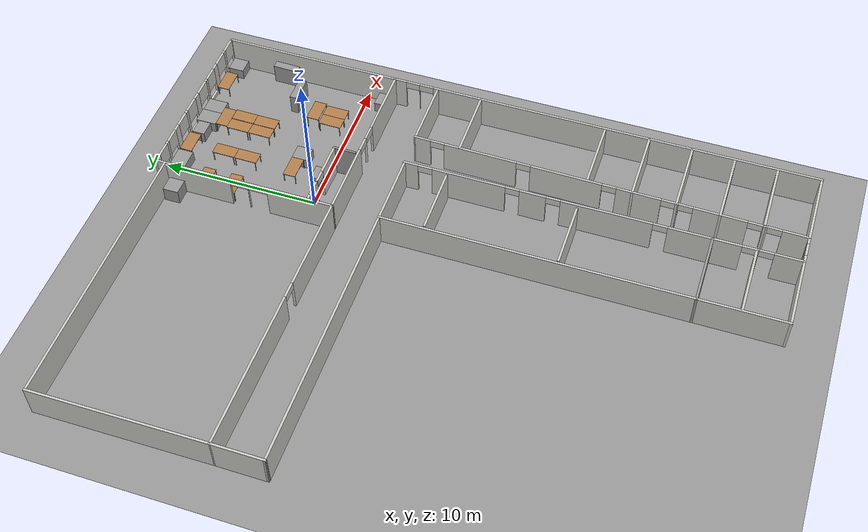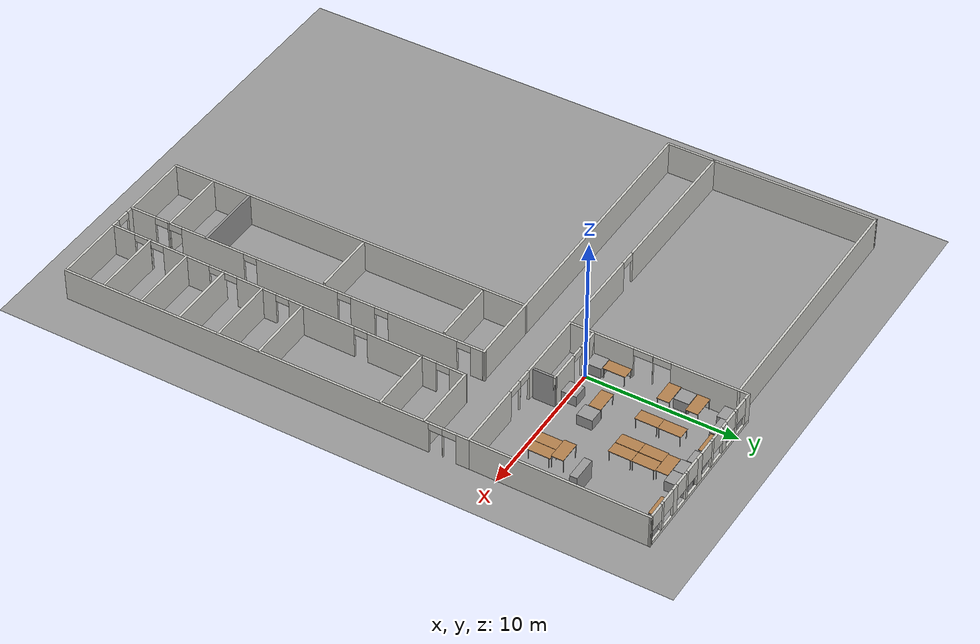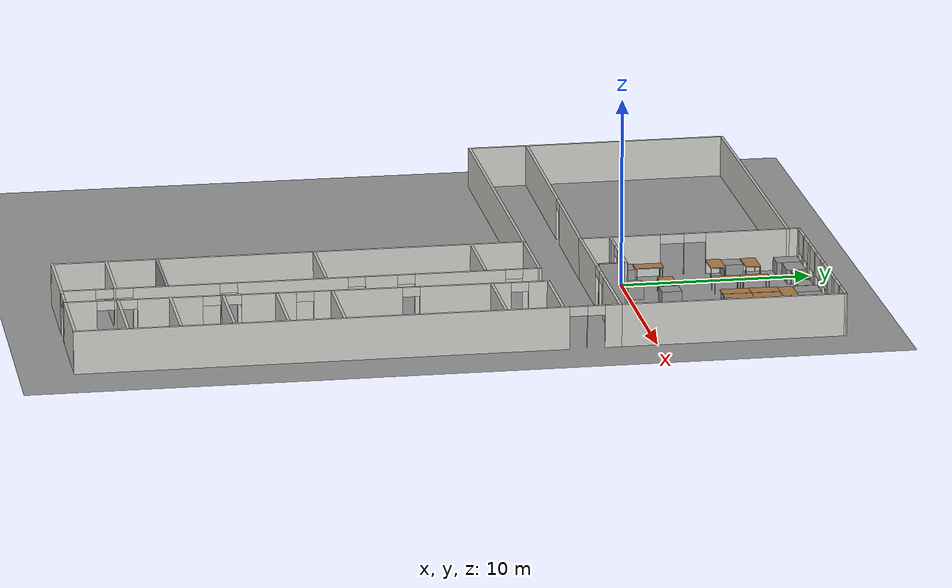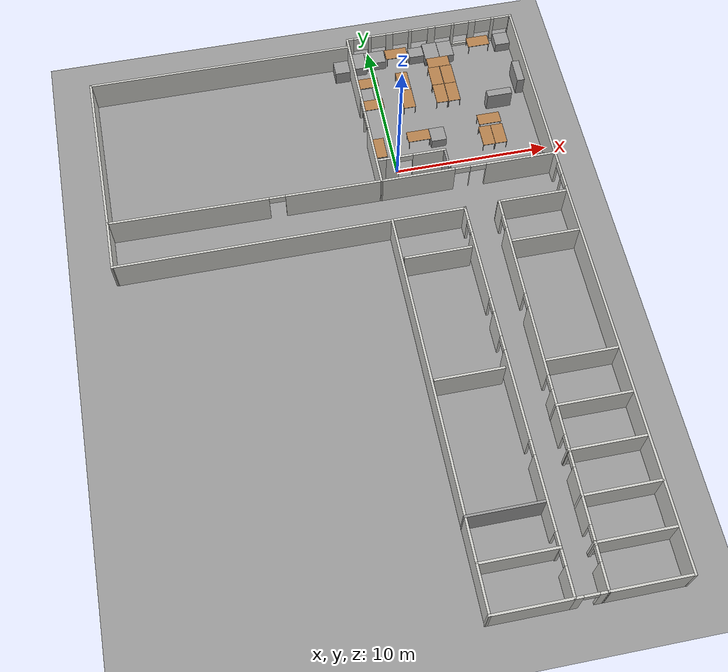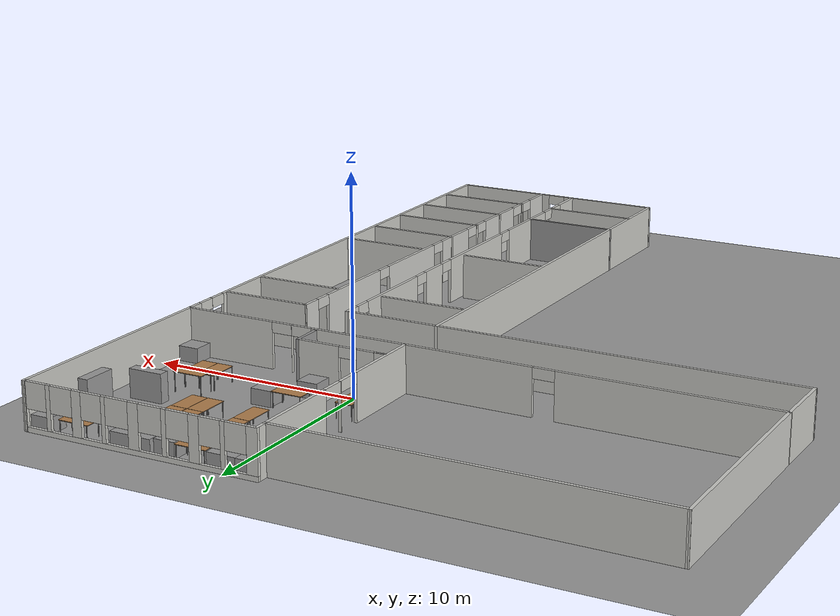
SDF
<?xml version='1.0'?>
<sdf version='1.7'>
  <model name='faps_model_features'>
    <link name='box_1'>
      <inertial>
        <mass>1</mass>
        <inertia>
          <ixx>0.166667</ixx>
          <ixy>0</ixy>
          <ixz>0</ixz>
          <iyy>0.166667</iyy>
          <iyz>0</iyz>
          <izz>0.166667</izz>
        </inertia>
      </inertial>
      <pose>-2.10854 8.4159 0.5 0 -0 0</pose>
      <visual name='visual'>
        <pose>0 0 0 0 -0 0</pose>
        <geometry>
          <box>
            <size>1 1 1</size>
          </box>
        </geometry>
        <material>
          <lighting>1</lighting>
          <script>
            <uri>file://media/materials/scripts/gazebo.material</uri>
            <name>Gazebo/Grey</name>
          </script>
          <shader type='pixel'/>
        </material>
        <transparency>0</transparency>
        <cast_shadows>1</cast_shadows>
      </visual>
      <collision name='collision'>
        <laser_retro>0</laser_retro>
        <max_contacts>10</max_contacts>
        <pose>0 0 0 0 -0 0</pose>
        <geometry>
          <box>
            <size>1 1 1</size>
          </box>
        </geometry>
        <surface>
          <friction>
            <ode>
              <mu>1</mu>
              <mu2>1</mu2>
              <fdir1>0 0 0</fdir1>
              <slip1>0</slip1>
              <slip2>0</slip2>
            </ode>
            <torsional>
              <coefficient>1</coefficient>
              <patch_radius>0</patch_radius>
              <surface_radius>0</surface_radius>
              <use_patch_radius>1</use_patch_radius>
              <ode>
                <slip>0</slip>
              </ode>
            </torsional>
          </friction>
          <bounce>
            <restitution_coefficient>0</restitution_coefficient>
            <threshold>1e+06</threshold>
          </bounce>
          <contact>
            <collide_without_contact>0</collide_without_contact>
            <collide_without_contact_bitmask>1</collide_without_contact_bitmask>
            <collide_bitmask>1</collide_bitmask>
            <ode>
              <soft_cfm>0</soft_cfm>
              <soft_erp>0.2</soft_erp>
              <kp>1e+13</kp>
              <kd>1</kd>
              <max_vel>0.01</max_vel>
              <min_depth>0</min_depth>
            </ode>
            <bullet>
              <split_impulse>1</split_impulse>
              <split_impulse_penetration_threshold>-0.01</split_impulse_penetration_threshold>
              <soft_cfm>0</soft_cfm>
              <soft_erp>0.2</soft_erp>
              <kp>1e+13</kp>
              <kd>1</kd>
            </bullet>
          </contact>
        </surface>
      </collision>
    </link>
    <model name='Untitled5'>
      <model name='FapsMap'>
        <link name='box_2'>
          <inertial>
            <mass>1</mass>
            <inertia>
              <ixx>0.166667</ixx>
              <ixy>0</ixy>
              <ixz>0</ixz>
              <iyy>0.166667</iyy>
              <iyz>0</iyz>
              <izz>0.166667</izz>
            </inertia>
          </inertial>
          <pose>1.86689 -5.60471 0.166667 0 -0 0</pose>
          <visual name='visual'>
            <pose>0 0 0 0 -0 0</pose>
            <geometry>
              <box>
                <size>1 1 1</size>
              </box>
            </geometry>
            <material>
              <lighting>1</lighting>
              <script>
                <uri>file://media/materials/scripts/gazebo.material</uri>
                <name>Gazebo/Grey</name>
              </script>
              <shader type='pixel'/>
            </material>
            <transparency>0</transparency>
            <cast_shadows>1</cast_shadows>
          </visual>
          <collision name='collision'>
            <laser_retro>0</laser_retro>
            <max_contacts>10</max_contacts>
            <pose>0 0 0 0 -0 0</pose>
            <geometry>
              <box>
                <size>1 1 1</size>
              </box>
            </geometry>
            <surface>
              <friction>
                <ode>
                  <mu>1</mu>
                  <mu2>1</mu2>
                  <fdir1>0 0 0</fdir1>
                  <slip1>0</slip1>
                  <slip2>0</slip2>
                </ode>
                <torsional>
                  <coefficient>1</coefficient>
                  <patch_radius>0</patch_radius>
                  <surface_radius>0</surface_radius>
                  <use_patch_radius>1</use_patch_radius>
                  <ode>
                    <slip>0</slip>
                  </ode>
                </torsional>
              </friction>
              <bounce>
                <restitution_coefficient>0</restitution_coefficient>
                <threshold>1e+06</threshold>
              </bounce>
              <contact>
                <collide_without_contact>0</collide_without_contact>
                <collide_without_contact_bitmask>1</collide_without_contact_bitmask>
                <collide_bitmask>1</collide_bitmask>
                <ode>
                  <soft_cfm>0</soft_cfm>
                  <soft_erp>0.2</soft_erp>
                  <kp>1e+13</kp>
                  <kd>1</kd>
                  <max_vel>0.01</max_vel>
                  <min_depth>0</min_depth>
                </ode>
                <bullet>
                  <split_impulse>1</split_impulse>
                  <split_impulse_penetration_threshold>-0.01</split_impulse_penetration_threshold>
                  <soft_cfm>0</soft_cfm>
                  <soft_erp>0.2</soft_erp>
                  <kp>1e+13</kp>
                  <kd>1</kd>
                </bullet>
              </contact>
            </surface>
          </collision>
        </link>
        <link name='box_3'>
          <inertial>
            <mass>1.87105</mass>
            <inertia>
              <ixx>0.841277</ixx>
              <ixy>0</ixy>
              <ixz>0</ixz>
              <iyy>1.22942</iyy>
              <iyz>0</iyz>
              <izz>0.4656</izz>
            </inertia>
            <pose>0 0 0 0 -0 0</pose>
          </inertial>
          <pose>0.432931 -0.185022 0.166667 0 -0 0</pose>
          <visual name='visual'>
            <pose>0 0 0 0 -0 0</pose>
            <geometry>
              <box>
                <size>1.65461 0.498377 2.26873</size>
              </box>
            </geometry>
            <material>
              <lighting>1</lighting>
              <script>
                <uri>file://media/materials/scripts/gazebo.material</uri>
                <name>Gazebo/Grey</name>
              </script>
              <shader type='pixel'/>
            </material>
            <transparency>0</transparency>
            <cast_shadows>1</cast_shadows>
          </visual>
          <collision name='collision'>
            <laser_retro>0</laser_retro>
            <max_contacts>10</max_contacts>
            <pose>0 0 0 0 -0 0</pose>
            <geometry>
              <box>
                <size>1.65461 0.498377 2.26873</size>
              </box>
            </geometry>
            <surface>
              <friction>
                <ode>
                  <mu>1</mu>
                  <mu2>1</mu2>
                  <fdir1>0 0 0</fdir1>
                  <slip1>0</slip1>
                  <slip2>0</slip2>
                </ode>
                <torsional>
                  <coefficient>1</coefficient>
                  <patch_radius>0</patch_radius>
                  <surface_radius>0</surface_radius>
                  <use_patch_radius>1</use_patch_radius>
                  <ode>
                    <slip>0</slip>
                  </ode>
                </torsional>
              </friction>
              <bounce>
                <restitution_coefficient>0</restitution_coefficient>
                <threshold>1e+06</threshold>
              </bounce>
              <contact>
                <collide_without_contact>0</collide_without_contact>
                <collide_without_contact_bitmask>1</collide_without_contact_bitmask>
                <collide_bitmask>1</collide_bitmask>
                <ode>
                  <soft_cfm>0</soft_cfm>
                  <soft_erp>0.2</soft_erp>
                  <kp>1e+13</kp>
                  <kd>1</kd>
                  <max_vel>0.01</max_vel>
                  <min_depth>0</min_depth>
                </ode>
                <bullet>
                  <split_impulse>1</split_impulse>
                  <split_impulse_penetration_threshold>-0.01</split_impulse_penetration_threshold>
                  <soft_cfm>0</soft_cfm>
                  <soft_erp>0.2</soft_erp>
                  <kp>1e+13</kp>
                  <kd>1</kd>
                </bullet>
              </contact>
            </surface>
          </collision>
        </link>
        <link name='box_3_clone'>
          <inertial>
            <mass>1.87105</mass>
            <inertia>
              <ixx>0.841277</ixx>
              <ixy>0</ixy>
              <ixz>0</ixz>
              <iyy>1.22942</iyy>
              <iyz>0</iyz>
              <izz>0.4656</izz>
            </inertia>
            <pose>0 0 0 0 -0 0</pose>
          </inertial>
          <pose>2.12837 1.31887 0.166667 0 -0 1.55522</pose>
          <visual name='visual'>
            <pose>0 0 0 0 -0 0</pose>
            <geometry>
              <box>
                <size>1.65461 0.498377 2.26873</size>
              </box>
            </geometry>
            <material>
              <lighting>1</lighting>
              <script>
                <uri>file://media/materials/scripts/gazebo.material</uri>
                <name>Gazebo/Grey</name>
              </script>
              <shader type='pixel'/>
            </material>
            <transparency>0</transparency>
            <cast_shadows>1</cast_shadows>
          </visual>
          <collision name='collision'>
            <laser_retro>0</laser_retro>
            <max_contacts>10</max_contacts>
            <pose>0 0 0 0 -0 0</pose>
            <geometry>
              <box>
                <size>1.65461 0.498377 2.26873</size>
              </box>
            </geometry>
            <surface>
              <friction>
                <ode>
                  <mu>1</mu>
                  <mu2>1</mu2>
                  <fdir1>0 0 0</fdir1>
                  <slip1>0</slip1>
                  <slip2>0</slip2>
                </ode>
                <torsional>
                  <coefficient>1</coefficient>
                  <patch_radius>0</patch_radius>
                  <surface_radius>0</surface_radius>
                  <use_patch_radius>1</use_patch_radius>
                  <ode>
                    <slip>0</slip>
                  </ode>
                </torsional>
              </friction>
              <bounce>
                <restitution_coefficient>0</restitution_coefficient>
                <threshold>1e+06</threshold>
              </bounce>
              <contact>
                <collide_without_contact>0</collide_without_contact>
                <collide_without_contact_bitmask>1</collide_without_contact_bitmask>
                <collide_bitmask>1</collide_bitmask>
                <ode>
                  <soft_cfm>0</soft_cfm>
                  <soft_erp>0.2</soft_erp>
                  <kp>1e+13</kp>
                  <kd>1</kd>
                  <max_vel>0.01</max_vel>
                  <min_depth>0</min_depth>
                </ode>
                <bullet>
                  <split_impulse>1</split_impulse>
                  <split_impulse_penetration_threshold>-0.01</split_impulse_penetration_threshold>
                  <soft_cfm>0</soft_cfm>
                  <soft_erp>0.2</soft_erp>
                  <kp>1e+13</kp>
                  <kd>1</kd>
                </bullet>
              </contact>
            </surface>
          </collision>
        </link>
        <link name='box_4'>
          <inertial>
            <mass>1</mass>
            <inertia>
              <ixx>0.166667</ixx>
              <ixy>0</ixy>
              <ixz>0</ixz>
              <iyy>0.166667</iyy>
              <iyz>0</iyz>
              <izz>0.166667</izz>
            </inertia>
          </inertial>
          <pose>1.88765 4.74942 0.166667 0 -0 0</pose>
          <visual name='visual'>
            <pose>0 0 0 0 -0 0</pose>
            <geometry>
              <box>
                <size>1 1 1</size>
              </box>
            </geometry>
            <material>
              <lighting>1</lighting>
              <script>
                <uri>file://media/materials/scripts/gazebo.material</uri>
                <name>Gazebo/Grey</name>
              </script>
              <shader type='pixel'/>
            </material>
            <transparency>0</transparency>
            <cast_shadows>1</cast_shadows>
          </visual>
          <collision name='collision'>
            <laser_retro>0</laser_retro>
            <max_contacts>10</max_contacts>
            <pose>0 0 0 0 -0 0</pose>
            <geometry>
              <box>
                <size>1 1 1</size>
              </box>
            </geometry>
            <surface>
              <friction>
                <ode>
                  <mu>1</mu>
                  <mu2>1</mu2>
                  <fdir1>0 0 0</fdir1>
                  <slip1>0</slip1>
                  <slip2>0</slip2>
                </ode>
                <torsional>
                  <coefficient>1</coefficient>
                  <patch_radius>0</patch_radius>
                  <surface_radius>0</surface_radius>
                  <use_patch_radius>1</use_patch_radius>
                  <ode>
                    <slip>0</slip>
                  </ode>
                </torsional>
              </friction>
              <bounce>
                <restitution_coefficient>0</restitution_coefficient>
                <threshold>1e+06</threshold>
              </bounce>
              <contact>
                <collide_without_contact>0</collide_without_contact>
                <collide_without_contact_bitmask>1</collide_without_contact_bitmask>
                <collide_bitmask>1</collide_bitmask>
                <ode>
                  <soft_cfm>0</soft_cfm>
                  <soft_erp>0.2</soft_erp>
                  <kp>1e+13</kp>
                  <kd>1</kd>
                  <max_vel>0.01</max_vel>
                  <min_depth>0</min_depth>
                </ode>
                <bullet>
                  <split_impulse>1</split_impulse>
                  <split_impulse_penetration_threshold>-0.01</split_impulse_penetration_threshold>
                  <soft_cfm>0</soft_cfm>
                  <soft_erp>0.2</soft_erp>
                  <kp>1e+13</kp>
                  <kd>1</kd>
                </bullet>
              </contact>
            </surface>
          </collision>
        </link>
        <model name='new_model2'>
          <link name='box_0'>
            <inertial>
              <mass>1</mass>
              <inertia>
                <ixx>0.166667</ixx>
                <ixy>0</ixy>
                <ixz>0</ixz>
                <iyy>0.166667</iyy>
                <iyz>0</iyz>
                <izz>0.166667</izz>
              </inertia>
            </inertial>
            <pose>-1.66046 1.09823 0.516468 0 -0 0</pose>
            <visual name='visual'>
              <pose>0 0 0 0 -0 0</pose>
              <geometry>
                <box>
                  <size>1 1 1</size>
                </box>
              </geometry>
              <material>
                <lighting>1</lighting>
                <script>
                  <uri>file://media/materials/scripts/gazebo.material</uri>
                  <name>Gazebo/Grey</name>
                </script>
                <shader type='pixel'/>
              </material>
              <transparency>0</transparency>
              <cast_shadows>1</cast_shadows>
            </visual>
            <collision name='collision'>
              <laser_retro>0</laser_retro>
              <max_contacts>10</max_contacts>
              <pose>0 0 0 0 -0 0</pose>
              <geometry>
                <box>
                  <size>1 1 1</size>
                </box>
              </geometry>
              <surface>
                <friction>
                  <ode>
                    <mu>1</mu>
                    <mu2>1</mu2>
                    <fdir1>0 0 0</fdir1>
                    <slip1>0</slip1>
                    <slip2>0</slip2>
                  </ode>
                  <torsional>
                    <coefficient>1</coefficient>
                    <patch_radius>0</patch_radius>
                    <surface_radius>0</surface_radius>
                    <use_patch_radius>1</use_patch_radius>
                    <ode>
                      <slip>0</slip>
                    </ode>
                  </torsional>
                </friction>
                <bounce>
                  <restitution_coefficient>0</restitution_coefficient>
                  <threshold>1e+06</threshold>
                </bounce>
                <contact>
                  <collide_without_contact>0</collide_without_contact>
                  <collide_without_contact_bitmask>1</collide_without_contact_bitmask>
                  <collide_bitmask>1</collide_bitmask>
                  <ode>
                    <soft_cfm>0</soft_cfm>
                    <soft_erp>0.2</soft_erp>
                    <kp>1e+13</kp>
                    <kd>1</kd>
                    <max_vel>0.01</max_vel>
                    <min_depth>0</min_depth>
                  </ode>
                  <bullet>
                    <split_impulse>1</split_impulse>
                    <split_impulse_penetration_threshold>-0.01</split_impulse_penetration_threshold>
                    <soft_cfm>0</soft_cfm>
                    <soft_erp>0.2</soft_erp>
                    <kp>1e+13</kp>
                    <kd>1</kd>
                  </bullet>
                </contact>
              </surface>
            </collision>
          </link>
          <link name='box_1'>
            <inertial>
              <mass>1</mass>
              <inertia>
                <ixx>0.166667</ixx>
                <ixy>0</ixy>
                <ixz>0</ixz>
                <iyy>0.166667</iyy>
                <iyz>0</iyz>
                <izz>0.166667</izz>
              </inertia>
            </inertial>
            <pose>1.10369 1.04984 0.516468 0 -0 0</pose>
            <visual name='visual'>
              <pose>0 0 0 0 -0 0</pose>
              <geometry>
                <box>
                  <size>1 1 1</size>
                </box>
              </geometry>
              <material>
                <lighting>1</lighting>
                <script>
                  <uri>file://media/materials/scripts/gazebo.material</uri>
                  <name>Gazebo/Grey</name>
                </script>
                <shader type='pixel'/>
              </material>
              <transparency>0</transparency>
              <cast_shadows>1</cast_shadows>
            </visual>
            <collision name='collision'>
              <laser_retro>0</laser_retro>
              <max_contacts>10</max_contacts>
              <pose>0 0 0 0 -0 0</pose>
              <geometry>
                <box>
                  <size>1 1 1</size>
                </box>
              </geometry>
              <surface>
                <friction>
                  <ode>
                    <mu>1</mu>
                    <mu2>1</mu2>
                    <fdir1>0 0 0</fdir1>
                    <slip1>0</slip1>
                    <slip2>0</slip2>
                  </ode>
                  <torsional>
                    <coefficient>1</coefficient>
                    <patch_radius>0</patch_radius>
                    <surface_radius>0</surface_radius>
                    <use_patch_radius>1</use_patch_radius>
                    <ode>
                      <slip>0</slip>
                    </ode>
                  </torsional>
                </friction>
                <bounce>
                  <restitution_coefficient>0</restitution_coefficient>
                  <threshold>1e+06</threshold>
                </bounce>
                <contact>
                  <collide_without_contact>0</collide_without_contact>
                  <collide_without_contact_bitmask>1</collide_without_contact_bitmask>
                  <collide_bitmask>1</collide_bitmask>
                  <ode>
                    <soft_cfm>0</soft_cfm>
                    <soft_erp>0.2</soft_erp>
                    <kp>1e+13</kp>
                    <kd>1</kd>
                    <max_vel>0.01</max_vel>
                    <min_depth>0</min_depth>
                  </ode>
                  <bullet>
                    <split_impulse>1</split_impulse>
                    <split_impulse_penetration_threshold>-0.01</split_impulse_penetration_threshold>
                    <soft_cfm>0</soft_cfm>
                    <soft_erp>0.2</soft_erp>
                    <kp>1e+13</kp>
                    <kd>1</kd>
                  </bullet>
                </contact>
              </surface>
            </collision>
          </link>
          <link name='box_2'>
            <inertial>
              <mass>1.03239</mass>
              <inertia>
                <ixx>0.177727</ixx>
                <ixy>0</ixy>
                <ixz>0</ixz>
                <iyy>0.172064</iyy>
                <iyz>0</iyz>
                <izz>0.177727</izz>
              </inertia>
              <pose>0 0 0 0 -0 0</pose>
            </inertial>
            <pose>2.33011 2.7769 0.516468 0 -0 0</pose>
            <visual name='visual'>
              <pose>0 0 0 0 -0 0</pose>
              <geometry>
                <box>
                  <size>1 1.03239 1</size>
                </box>
              </geometry>
              <material>
                <lighting>1</lighting>
                <script>
                  <uri>file://media/materials/scripts/gazebo.material</uri>
                  <name>Gazebo/Grey</name>
                </script>
                <shader type='pixel'/>
              </material>
              <transparency>0</transparency>
              <cast_shadows>1</cast_shadows>
            </visual>
            <collision name='collision'>
              <laser_retro>0</laser_retro>
              <max_contacts>10</max_contacts>
              <pose>0 0 0 0 -0 0</pose>
              <geometry>
                <box>
                  <size>1 1.03239 1</size>
                </box>
              </geometry>
              <surface>
                <friction>
                  <ode>
                    <mu>1</mu>
                    <mu2>1</mu2>
                    <fdir1>0 0 0</fdir1>
                    <slip1>0</slip1>
                    <slip2>0</slip2>
                  </ode>
                  <torsional>
                    <coefficient>1</coefficient>
                    <patch_radius>0</patch_radius>
                    <surface_radius>0</surface_radius>
                    <use_patch_radius>1</use_patch_radius>
                    <ode>
                      <slip>0</slip>
                    </ode>
                  </torsional>
                </friction>
                <bounce>
                  <restitution_coefficient>0</restitution_coefficient>
                  <threshold>1e+06</threshold>
                </bounce>
                <contact>
                  <collide_without_contact>0</collide_without_contact>
                  <collide_without_contact_bitmask>1</collide_without_contact_bitmask>
                  <collide_bitmask>1</collide_bitmask>
                  <ode>
                    <soft_cfm>0</soft_cfm>
                    <soft_erp>0.2</soft_erp>
                    <kp>1e+13</kp>
                    <kd>1</kd>
                    <max_vel>0.01</max_vel>
                    <min_depth>0</min_depth>
                  </ode>
                  <bullet>
                    <split_impulse>1</split_impulse>
                    <split_impulse_penetration_threshold>-0.01</split_impulse_penetration_threshold>
                    <soft_cfm>0</soft_cfm>
                    <soft_erp>0.2</soft_erp>
                    <kp>1e+13</kp>
                    <kd>1</kd>
                  </bullet>
                </contact>
              </surface>
            </collision>
          </link>
          <link name='box_3'>
            <inertial>
              <mass>1</mass>
              <inertia>
                <ixx>0.166667</ixx>
                <ixy>0</ixy>
                <ixz>0</ixz>
                <iyy>0.166667</iyy>
                <iyz>0</iyz>
                <izz>0.166667</izz>
              </inertia>
            </inertial>
            <pose>-1.68316 6.81972 0.516468 0 -0 0</pose>
            <visual name='visual'>
              <pose>0 0 0 0 -0 0</pose>
              <geometry>
                <box>
                  <size>1 1 1</size>
                </box>
              </geometry>
              <material>
                <lighting>1</lighting>
                <script>
                  <uri>file://media/materials/scripts/gazebo.material</uri>
                  <name>Gazebo/Grey</name>
                </script>
                <shader type='pixel'/>
              </material>
              <transparency>0</transparency>
              <cast_shadows>1</cast_shadows>
            </visual>
            <collision name='collision'>
              <laser_retro>0</laser_retro>
              <max_contacts>10</max_contacts>
              <pose>0 0 0 0 -0 0</pose>
              <geometry>
                <box>
                  <size>1 1 1</size>
                </box>
              </geometry>
              <surface>
                <friction>
                  <ode>
                    <mu>1</mu>
                    <mu2>1</mu2>
                    <fdir1>0 0 0</fdir1>
                    <slip1>0</slip1>
                    <slip2>0</slip2>
                  </ode>
                  <torsional>
                    <coefficient>1</coefficient>
                    <patch_radius>0</patch_radius>
                    <surface_radius>0</surface_radius>
                    <use_patch_radius>1</use_patch_radius>
                    <ode>
                      <slip>0</slip>
                    </ode>
                  </torsional>
                </friction>
                <bounce>
                  <restitution_coefficient>0</restitution_coefficient>
                  <threshold>1e+06</threshold>
                </bounce>
                <contact>
                  <collide_without_contact>0</collide_without_contact>
                  <collide_without_contact_bitmask>1</collide_without_contact_bitmask>
                  <collide_bitmask>1</collide_bitmask>
                  <ode>
                    <soft_cfm>0</soft_cfm>
                    <soft_erp>0.2</soft_erp>
                    <kp>1e+13</kp>
                    <kd>1</kd>
                    <max_vel>0.01</max_vel>
                    <min_depth>0</min_depth>
                  </ode>
                  <bullet>
                    <split_impulse>1</split_impulse>
                    <split_impulse_penetration_threshold>-0.01</split_impulse_penetration_threshold>
                    <soft_cfm>0</soft_cfm>
                    <soft_erp>0.2</soft_erp>
                    <kp>1e+13</kp>
                    <kd>1</kd>
                  </bullet>
                </contact>
              </surface>
            </collision>
          </link>
          <link name='box_4'>
            <inertial>
              <mass>1.28316</mass>
              <inertia>
                <ixx>0.282993</ixx>
                <ixy>0</ixy>
                <ixz>0</ixz>
                <iyy>0.213861</iyy>
                <iyz>0</iyz>
                <izz>0.282993</izz>
              </inertia>
              <pose>0 0 0 0 -0 0</pose>
            </inertial>
            <pose>-1.65758 9.75819 0.516468 0 -0 0</pose>
            <visual name='visual'>
              <pose>0 0 0 0 -0 0</pose>
              <geometry>
                <box>
                  <size>1 1.28317 1</size>
                </box>
              </geometry>
              <material>
                <lighting>1</lighting>
                <script>
                  <uri>file://media/materials/scripts/gazebo.material</uri>
                  <name>Gazebo/Grey</name>
                </script>
                <shader type='pixel'/>
              </material>
              <transparency>0</transparency>
              <cast_shadows>1</cast_shadows>
            </visual>
            <collision name='collision'>
              <laser_retro>0</laser_retro>
              <max_contacts>10</max_contacts>
              <pose>0 0 0 0 -0 0</pose>
              <geometry>
                <box>
                  <size>1 1.28317 1</size>
                </box>
              </geometry>
              <surface>
                <friction>
                  <ode>
                    <mu>1</mu>
                    <mu2>1</mu2>
                    <fdir1>0 0 0</fdir1>
                    <slip1>0</slip1>
                    <slip2>0</slip2>
                  </ode>
                  <torsional>
                    <coefficient>1</coefficient>
                    <patch_radius>0</patch_radius>
                    <surface_radius>0</surface_radius>
                    <use_patch_radius>1</use_patch_radius>
                    <ode>
                      <slip>0</slip>
                    </ode>
                  </torsional>
                </friction>
                <bounce>
                  <restitution_coefficient>0</restitution_coefficient>
                  <threshold>1e+06</threshold>
                </bounce>
                <contact>
                  <collide_without_contact>0</collide_without_contact>
                  <collide_without_contact_bitmask>1</collide_without_contact_bitmask>
                  <collide_bitmask>1</collide_bitmask>
                  <ode>
                    <soft_cfm>0</soft_cfm>
                    <soft_erp>0.2</soft_erp>
                    <kp>1e+13</kp>
                    <kd>1</kd>
                    <max_vel>0.01</max_vel>
                    <min_depth>0</min_depth>
                  </ode>
                  <bullet>
                    <split_impulse>1</split_impulse>
                    <split_impulse_penetration_threshold>-0.01</split_impulse_penetration_threshold>
                    <soft_cfm>0</soft_cfm>
                    <soft_erp>0.2</soft_erp>
                    <kp>1e+13</kp>
                    <kd>1</kd>
                  </bullet>
                </contact>
              </surface>
            </collision>
          </link>
          <link name='box_5'>
            <inertial>
              <mass>1.37081</mass>
              <inertia>
                <ixx>0.228469</ixx>
                <ixy>0</ixy>
                <ixz>0</ixz>
                <iyy>0.328897</iyy>
                <iyz>0</iyz>
                <izz>0.328897</izz>
              </inertia>
              <pose>0 0 0 0 -0 0</pose>
            </inertial>
            <pose>-0.475085 9.87452 0.516468 0 -0 0</pose>
            <visual name='visual'>
              <pose>0 0 0 0 -0 0</pose>
              <geometry>
                <box>
                  <size>1.37082 1 1</size>
                </box>
              </geometry>
              <material>
                <lighting>1</lighting>
                <script>
                  <uri>file://media/materials/scripts/gazebo.material</uri>
                  <name>Gazebo/Grey</name>
                </script>
                <shader type='pixel'/>
              </material>
              <transparency>0</transparency>
              <cast_shadows>1</cast_shadows>
            </visual>
            <collision name='collision'>
              <laser_retro>0</laser_retro>
              <max_contacts>10</max_contacts>
              <pose>0 0 0 0 -0 0</pose>
              <geometry>
                <box>
                  <size>1.37082 1 1</size>
                </box>
              </geometry>
              <surface>
                <friction>
                  <ode>
                    <mu>1</mu>
                    <mu2>1</mu2>
                    <fdir1>0 0 0</fdir1>
                    <slip1>0</slip1>
                    <slip2>0</slip2>
                  </ode>
                  <torsional>
                    <coefficient>1</coefficient>
                    <patch_radius>0</patch_radius>
                    <surface_radius>0</surface_radius>
                    <use_patch_radius>1</use_patch_radius>
                    <ode>
                      <slip>0</slip>
                    </ode>
                  </torsional>
                </friction>
                <bounce>
                  <restitution_coefficient>0</restitution_coefficient>
                  <threshold>1e+06</threshold>
                </bounce>
                <contact>
                  <collide_without_contact>0</collide_without_contact>
                  <collide_without_contact_bitmask>1</collide_without_contact_bitmask>
                  <collide_bitmask>1</collide_bitmask>
                  <ode>
                    <soft_cfm>0</soft_cfm>
                    <soft_erp>0.2</soft_erp>
                    <kp>1e+13</kp>
                    <kd>1</kd>
                    <max_vel>0.01</max_vel>
                    <min_depth>0</min_depth>
                  </ode>
                  <bullet>
                    <split_impulse>1</split_impulse>
                    <split_impulse_penetration_threshold>-0.01</split_impulse_penetration_threshold>
                    <soft_cfm>0</soft_cfm>
                    <soft_erp>0.2</soft_erp>
                    <kp>1e+13</kp>
                    <kd>1</kd>
                  </bullet>
                </contact>
              </surface>
            </collision>
          </link>
          <link name='box_7'>
            <inertial>
              <mass>0.793101</mass>
              <inertia>
                <ixx>0.107664</ixx>
                <ixy>0</ixy>
                <ixz>0</ixz>
                <iyy>0.132183</iyy>
                <iyz>0</iyz>
                <izz>0.107664</izz>
              </inertia>
              <pose>0 0 0 0 -0 0</pose>
            </inertial>
            <pose>2.37708 9.78834 0.516468 0 -0 0</pose>
            <visual name='visual'>
              <pose>0 0 0 0 -0 0</pose>
              <geometry>
                <box>
                  <size>1 0.7931 1</size>
                </box>
              </geometry>
              <material>
                <lighting>1</lighting>
                <script>
                  <uri>file://media/materials/scripts/gazebo.material</uri>
                  <name>Gazebo/Grey</name>
                </script>
                <shader type='pixel'/>
              </material>
              <transparency>0</transparency>
              <cast_shadows>1</cast_shadows>
            </visual>
            <collision name='collision'>
              <laser_retro>0</laser_retro>
              <max_contacts>10</max_contacts>
              <pose>0 0 0 0 -0 0</pose>
              <geometry>
                <box>
                  <size>1 0.7931 1</size>
                </box>
              </geometry>
              <surface>
                <friction>
                  <ode>
                    <mu>1</mu>
                    <mu2>1</mu2>
                    <fdir1>0 0 0</fdir1>
                    <slip1>0</slip1>
                    <slip2>0</slip2>
                  </ode>
                  <torsional>
                    <coefficient>1</coefficient>
                    <patch_radius>0</patch_radius>
                    <surface_radius>0</surface_radius>
                    <use_patch_radius>1</use_patch_radius>
                    <ode>
                      <slip>0</slip>
                    </ode>
                  </torsional>
                </friction>
                <bounce>
                  <restitution_coefficient>0</restitution_coefficient>
                  <threshold>1e+06</threshold>
                </bounce>
                <contact>
                  <collide_without_contact>0</collide_without_contact>
                  <collide_without_contact_bitmask>1</collide_without_contact_bitmask>
                  <collide_bitmask>1</collide_bitmask>
                  <ode>
                    <soft_cfm>0</soft_cfm>
                    <soft_erp>0.2</soft_erp>
                    <kp>1e+13</kp>
                    <kd>1</kd>
                    <max_vel>0.01</max_vel>
                    <min_depth>0</min_depth>
                  </ode>
                  <bullet>
                    <split_impulse>1</split_impulse>
                    <split_impulse_penetration_threshold>-0.01</split_impulse_penetration_threshold>
                    <soft_cfm>0</soft_cfm>
                    <soft_erp>0.2</soft_erp>
                    <kp>1e+13</kp>
                    <kd>1</kd>
                  </bullet>
                </contact>
              </surface>
            </collision>
          </link>
          <link name='box_8'>
            <inertial>
              <mass>1.31027</mass>
              <inertia>
                <ixx>0.296645</ixx>
                <ixy>0</ixy>
                <ixz>0</ixz>
                <iyy>0.218378</iyy>
                <iyz>0</iyz>
                <izz>0.296645</izz>
              </inertia>
              <pose>0 0 0 0 -0 0</pose>
            </inertial>
            <pose>3.40898 9.72838 0.516468 0 -0 0</pose>
            <visual name='visual'>
              <pose>0 0 0 0 -0 0</pose>
              <geometry>
                <box>
                  <size>1 1.31027 1</size>
                </box>
              </geometry>
              <material>
                <lighting>1</lighting>
                <script>
                  <uri>file://media/materials/scripts/gazebo.material</uri>
                  <name>Gazebo/Grey</name>
                </script>
                <shader type='pixel'/>
              </material>
              <transparency>0</transparency>
              <cast_shadows>1</cast_shadows>
            </visual>
            <collision name='collision'>
              <laser_retro>0</laser_retro>
              <max_contacts>10</max_contacts>
              <pose>0 0 0 0 -0 0</pose>
              <geometry>
                <box>
                  <size>1 1.31027 1</size>
                </box>
              </geometry>
              <surface>
                <friction>
                  <ode>
                    <mu>1</mu>
                    <mu2>1</mu2>
                    <fdir1>0 0 0</fdir1>
                    <slip1>0</slip1>
                    <slip2>0</slip2>
                  </ode>
                  <torsional>
                    <coefficient>1</coefficient>
                    <patch_radius>0</patch_radius>
                    <surface_radius>0</surface_radius>
                    <use_patch_radius>1</use_patch_radius>
                    <ode>
                      <slip>0</slip>
                    </ode>
                  </torsional>
                </friction>
                <bounce>
                  <restitution_coefficient>0</restitution_coefficient>
                  <threshold>1e+06</threshold>
                </bounce>
                <contact>
                  <collide_without_contact>0</collide_without_contact>
                  <collide_without_contact_bitmask>1</collide_without_contact_bitmask>
                  <collide_bitmask>1</collide_bitmask>
                  <ode>
                    <soft_cfm>0</soft_cfm>
                    <soft_erp>0.2</soft_erp>
                    <kp>1e+13</kp>
                    <kd>1</kd>
                    <max_vel>0.01</max_vel>
                    <min_depth>0</min_depth>
                  </ode>
                  <bullet>
                    <split_impulse>1</split_impulse>
                    <split_impulse_penetration_threshold>-0.01</split_impulse_penetration_threshold>
                    <soft_cfm>0</soft_cfm>
                    <soft_erp>0.2</soft_erp>
                    <kp>1e+13</kp>
                    <kd>1</kd>
                  </bullet>
                </contact>
              </surface>
            </collision>
          </link>
          <link name='box_9'>
            <inertial>
              <mass>1.28236</mass>
              <inertia>
                <ixx>0.282593</ixx>
                <ixy>0</ixy>
                <ixz>0</ixz>
                <iyy>0.213727</iyy>
                <iyz>0</iyz>
                <izz>0.282593</izz>
              </inertia>
              <pose>0 0 0 0 -0 0</pose>
            </inertial>
            <pose>4.41567 9.70967 0.516468 0 -0 0</pose>
            <visual name='visual'>
              <pose>0 0 0 0 -0 0</pose>
              <geometry>
                <box>
                  <size>1 1.28235 1</size>
                </box>
              </geometry>
              <material>
                <lighting>1</lighting>
                <script>
                  <uri>file://media/materials/scripts/gazebo.material</uri>
                  <name>Gazebo/Grey</name>
                </script>
                <shader type='pixel'/>
              </material>
              <transparency>0</transparency>
              <cast_shadows>1</cast_shadows>
            </visual>
            <collision name='collision'>
              <laser_retro>0</laser_retro>
              <max_contacts>10</max_contacts>
              <pose>0 0 0 0 -0 0</pose>
              <geometry>
                <box>
                  <size>1 1.28235 1</size>
                </box>
              </geometry>
              <surface>
                <friction>
                  <ode>
                    <mu>1</mu>
                    <mu2>1</mu2>
                    <fdir1>0 0 0</fdir1>
                    <slip1>0</slip1>
                    <slip2>0</slip2>
                  </ode>
                  <torsional>
                    <coefficient>1</coefficient>
                    <patch_radius>0</patch_radius>
                    <surface_radius>0</surface_radius>
                    <use_patch_radius>1</use_patch_radius>
                    <ode>
                      <slip>0</slip>
                    </ode>
                  </torsional>
                </friction>
                <bounce>
                  <restitution_coefficient>0</restitution_coefficient>
                  <threshold>1e+06</threshold>
                </bounce>
                <contact>
                  <collide_without_contact>0</collide_without_contact>
                  <collide_without_contact_bitmask>1</collide_without_contact_bitmask>
                  <collide_bitmask>1</collide_bitmask>
                  <ode>
                    <soft_cfm>0</soft_cfm>
                    <soft_erp>0.2</soft_erp>
                    <kp>1e+13</kp>
                    <kd>1</kd>
                    <max_vel>0.01</max_vel>
                    <min_depth>0</min_depth>
                  </ode>
                  <bullet>
                    <split_impulse>1</split_impulse>
                    <split_impulse_penetration_threshold>-0.01</split_impulse_penetration_threshold>
                    <soft_cfm>0</soft_cfm>
                    <soft_erp>0.2</soft_erp>
                    <kp>1e+13</kp>
                    <kd>1</kd>
                  </bullet>
                </contact>
              </surface>
            </collision>
          </link>
          <model name='FapsModel'>
            <pose>-5.26511 -9.10909 0.016468 0 -0 0</pose>
            <link name='Wall_1'>
              <collision name='Wall_1_Collision'>
                <geometry>
                  <box>
                    <size>11.7388 0.15 2.5</size>
                  </box>
                </geometry>
                <pose>0 0 1.25 0 -0 0</pose>
              </collision>
              <visual name='Wall_1_Visual'>
                <pose>0 0 1.25 0 -0 0</pose>
                <geometry>
                  <box>
                    <size>11.7388 0.15 2.5</size>
                  </box>
                </geometry>
                <material>
                  <script>
                    <uri>file://media/materials/scripts/gazebo.material</uri>
                    <name>Gazebo/CeilingTiled</name>
                  </script>
                  <ambient>1 1 1 1</ambient>
                </material>
                <meta>
                  <layer>0</layer>
                </meta>
              </visual>
              <pose>14.3214 13.8027 0 0 -0 1.56589</pose>
            </link>
            <link name='Wall_113'>
              <collision name='Wall_113_Collision'>
                <geometry>
                  <box>
                    <size>3.30454 0.15 2.5</size>
                  </box>
                </geometry>
                <pose>0 0 1.25 0 -0 0</pose>
              </collision>
              <visual name='Wall_113_Visual'>
                <pose>0 0 1.25 0 -0 0</pose>
                <geometry>
                  <box>
                    <size>3.30454 0.15 2.5</size>
                  </box>
                </geometry>
                <material>
                  <script>
                    <uri>file://media/materials/scripts/gazebo.material</uri>
                    <name>Gazebo/CeilingTiled</name>
                  </script>
                  <ambient>1 1 1 1</ambient>
                </material>
                <meta>
                  <layer>0</layer>
                </meta>
              </visual>
              <pose>-14.2575 6.56747 0 0 -0 -1.57202</pose>
            </link>
            <link name='Wall_16'>
              <collision name='Wall_16_Collision'>
                <geometry>
                  <box>
                    <size>11.0154 0.15 2.5</size>
                  </box>
                </geometry>
                <pose>0 0 1.25 0 -0 0</pose>
              </collision>
              <visual name='Wall_16_Visual'>
                <pose>0 0 1.25 0 -0 0</pose>
                <geometry>
                  <box>
                    <size>11.0154 0.15 2.5</size>
                  </box>
                </geometry>
                <material>
                  <script>
                    <uri>file://media/materials/scripts/gazebo.material</uri>
                    <name>Gazebo/CeilingTiled</name>
                  </script>
                  <ambient>1 1 1 1</ambient>
                </material>
                <meta>
                  <layer>0</layer>
                </meta>
              </visual>
              <pose>-14.3026 13.5773 0 0 -0 1.57945</pose>
            </link>
            <link name='Wall_17'>
              <collision name='Wall_17_Collision'>
                <geometry>
                  <box>
                    <size>17.5 0.15 2.5</size>
                  </box>
                </geometry>
                <pose>0 0 1.25 0 -0 0</pose>
              </collision>
              <visual name='Wall_17_Visual'>
                <pose>0 0 1.25 0 -0 0</pose>
                <geometry>
                  <box>
                    <size>17.5 0.15 2.5</size>
                  </box>
                </geometry>
                <material>
                  <script>
                    <uri>file://media/materials/scripts/gazebo.material</uri>
                    <name>Gazebo/CeilingTiled</name>
                  </script>
                  <ambient>1 1 1 1</ambient>
                </material>
                <meta>
                  <layer>0</layer>
                </meta>
              </visual>
              <pose>-5.67083 19.0098 0 0 -0 0</pose>
            </link>
            <link name='Wall_19'>
              <collision name='Wall_19_Collision'>
                <geometry>
                  <box>
                    <size>4.5 0.15 2.5</size>
                  </box>
                </geometry>
                <pose>0 0 1.25 0 -0 0</pose>
              </collision>
              <visual name='Wall_19_Visual'>
                <pose>0 0 1.25 0 -0 0</pose>
                <geometry>
                  <box>
                    <size>4.5 0.15 2.5</size>
                  </box>
                </geometry>
                <material>
                  <script>
                    <uri>file://media/materials/scripts/gazebo.material</uri>
                    <name>Gazebo/CeilingTiled</name>
                  </script>
                  <ambient>1 1 1 1</ambient>
                </material>
                <meta>
                  <layer>0</layer>
                </meta>
              </visual>
              <pose>12.0644 5.08895 0 0 -0 3.14159</pose>
            </link>
            <link name='Wall_20'>
              <pose>9.71758 -7.24949 0 0 -0 -1.58472</pose>
              <visual name='Wall_20_Visual_0'>
                <pose>-11.8689 0 1.25 0 -0 0</pose>
                <geometry>
                  <box>
                    <size>1.09097 0.15 2.5</size>
                  </box>
                </geometry>
                <material>
                  <script>
                    <uri>file://media/materials/scripts/gazebo.material</uri>
                    <name>Gazebo/CeilingTiled</name>
                  </script>
                  <ambient>1 1 1 1</ambient>
                </material>
                <meta>
                  <layer>0</layer>
                </meta>
              </visual>
              <collision name='Wall_20_Collision_0'>
                <geometry>
                  <box>
                    <size>1.09097 0.15 2.5</size>
                  </box>
                </geometry>
                <pose>-11.8689 0 1.25 0 -0 0</pose>
              </collision>
              <visual name='Wall_20_Visual_1'>
                <pose>-8.07474 0 1.25 0 -0 0</pose>
                <geometry>
                  <box>
                    <size>4.69725 0.15 2.5</size>
                  </box>
                </geometry>
                <material>
                  <script>
                    <uri>file://media/materials/scripts/gazebo.material</uri>
                    <name>Gazebo/CeilingTiled</name>
                  </script>
                  <ambient>1 1 1 1</ambient>
                </material>
                <meta>
                  <layer>0</layer>
                </meta>
              </visual>
              <collision name='Wall_20_Collision_1'>
                <geometry>
                  <box>
                    <size>4.69725 0.15 2.5</size>
                  </box>
                </geometry>
                <pose>-8.07474 0 1.25 0 -0 0</pose>
              </collision>
              <visual name='Wall_20_Visual_2'>
                <pose>-2.55992 0 1.25 0 -0 0</pose>
                <geometry>
                  <box>
                    <size>4.53239 0.15 2.5</size>
                  </box>
                </geometry>
                <material>
                  <script>
                    <uri>file://media/materials/scripts/gazebo.material</uri>
                    <name>Gazebo/CeilingTiled</name>
                  </script>
                  <ambient>1 1 1 1</ambient>
                </material>
                <meta>
                  <layer>0</layer>
                </meta>
              </visual>
              <collision name='Wall_20_Collision_2'>
                <geometry>
                  <box>
                    <size>4.53239 0.15 2.5</size>
                  </box>
                </geometry>
                <pose>-2.55992 0 1.25 0 -0 0</pose>
              </collision>
              <visual name='Wall_20_Visual_3'>
                <pose>1.99995 0 1.25 0 -0 0</pose>
                <geometry>
                  <box>
                    <size>2.78735 0.15 2.5</size>
                  </box>
                </geometry>
                <material>
                  <script>
                    <uri>file://media/materials/scripts/gazebo.material</uri>
                    <name>Gazebo/CeilingTiled</name>
                  </script>
                  <ambient>1 1 1 1</ambient>
                </material>
                <meta>
                  <layer>0</layer>
                </meta>
              </visual>
              <collision name='Wall_20_Collision_3'>
                <geometry>
                  <box>
                    <size>2.78735 0.15 2.5</size>
                  </box>
                </geometry>
                <pose>1.99995 0 1.25 0 -0 0</pose>
              </collision>
              <visual name='Wall_20_Visual_4'>
                <pose>4.37423 0 1.25 0 -0 0</pose>
                <geometry>
                  <box>
                    <size>0.161222 0.15 2.5</size>
                  </box>
                </geometry>
                <material>
                  <script>
                    <uri>file://media/materials/scripts/gazebo.material</uri>
                    <name>Gazebo/CeilingTiled</name>
                  </script>
                  <ambient>1 1 1 1</ambient>
                </material>
                <meta>
                  <layer>0</layer>
                </meta>
              </visual>
              <collision name='Wall_20_Collision_4'>
                <geometry>
                  <box>
                    <size>0.161222 0.15 2.5</size>
                  </box>
                </geometry>
                <pose>4.37423 0 1.25 0 -0 0</pose>
              </collision>
              <visual name='Wall_20_Visual_5'>
                <pose>7.01378 0 1.25 0 -0 0</pose>
                <geometry>
                  <box>
                    <size>3.31787 0.15 2.5</size>
                  </box>
                </geometry>
                <material>
                  <script>
                    <uri>file://media/materials/scripts/gazebo.material</uri>
                    <name>Gazebo/CeilingTiled</name>
                  </script>
                  <ambient>1 1 1 1</ambient>
                </material>
                <meta>
                  <layer>0</layer>
                </meta>
              </visual>
              <collision name='Wall_20_Collision_5'>
                <geometry>
                  <box>
                    <size>3.31787 0.15 2.5</size>
                  </box>
                </geometry>
                <pose>7.01378 0 1.25 0 -0 0</pose>
              </collision>
              <visual name='Wall_20_Visual_6'>
                <pose>9.70622 0 1.25 0 -0 0</pose>
                <geometry>
                  <box>
                    <size>0.267002 0.15 2.5</size>
                  </box>
                </geometry>
                <material>
                  <script>
                    <uri>file://media/materials/scripts/gazebo.material</uri>
                    <name>Gazebo/CeilingTiled</name>
                  </script>
                  <ambient>1 1 1 1</ambient>
                </material>
                <meta>
                  <layer>0</layer>
                </meta>
              </visual>
              <collision name='Wall_20_Collision_6'>
                <geometry>
                  <box>
                    <size>0.267002 0.15 2.5</size>
                  </box>
                </geometry>
                <pose>9.70622 0 1.25 0 -0 0</pose>
              </collision>
              <visual name='Wall_20_Visual_7'>
                <pose>11.577 0 1.25 0 -0 0</pose>
                <geometry>
                  <box>
                    <size>1.67461 0.15 2.5</size>
                  </box>
                </geometry>
                <material>
                  <script>
                    <uri>file://media/materials/scripts/gazebo.material</uri>
                    <name>Gazebo/CeilingTiled</name>
                  </script>
                  <ambient>1 1 1 1</ambient>
                </material>
                <meta>
                  <layer>0</layer>
                </meta>
              </visual>
              <collision name='Wall_20_Collision_7'>
                <geometry>
                  <box>
                    <size>1.67461 0.15 2.5</size>
                  </box>
                </geometry>
                <pose>11.577 0 1.25 0 -0 0</pose>
              </collision>
              <visual name='Wall_20_Visual_8'>
                <pose>-10.8734 0 2.25 0 -0 0</pose>
                <geometry>
                  <box>
                    <size>0.9 0.15 0.5</size>
                  </box>
                </geometry>
                <material>
                  <script>
                    <uri>file://media/materials/scripts/gazebo.material</uri>
                    <name>Gazebo/CeilingTiled</name>
                  </script>
                  <ambient>1 1 1 1</ambient>
                </material>
                <meta>
                  <layer>0</layer>
                </meta>
              </visual>
              <collision name='Wall_20_Collision_8'>
                <geometry>
                  <box>
                    <size>0.9 0.15 0.5</size>
                  </box>
                </geometry>
                <pose>-10.8734 0 2.25 0 -0 0</pose>
              </collision>
              <visual name='Wall_20_Visual_9'>
                <pose>-5.27611 0 2.25 0 -0 0</pose>
                <geometry>
                  <box>
                    <size>0.9 0.15 0.5</size>
                  </box>
                </geometry>
                <material>
                  <script>
                    <uri>file://media/materials/scripts/gazebo.material</uri>
                    <name>Gazebo/CeilingTiled</name>
                  </script>
                  <ambient>1 1 1 1</ambient>
                </material>
                <meta>
                  <layer>0</layer>
                </meta>
              </visual>
              <collision name='Wall_20_Collision_9'>
                <geometry>
                  <box>
                    <size>0.9 0.15 0.5</size>
                  </box>
                </geometry>
                <pose>-5.27611 0 2.25 0 -0 0</pose>
              </collision>
              <visual name='Wall_20_Visual_10'>
                <pose>0.156279 0 2.25 0 -0 0</pose>
                <geometry>
                  <box>
                    <size>0.9 0.15 0.5</size>
                  </box>
                </geometry>
                <material>
                  <script>
                    <uri>file://media/materials/scripts/gazebo.material</uri>
                    <name>Gazebo/CeilingTiled</name>
                  </script>
                  <ambient>1 1 1 1</ambient>
                </material>
                <meta>
                  <layer>0</layer>
                </meta>
              </visual>
              <collision name='Wall_20_Collision_10'>
                <geometry>
                  <box>
                    <size>0.9 0.15 0.5</size>
                  </box>
                </geometry>
                <pose>0.156279 0 2.25 0 -0 0</pose>
              </collision>
              <visual name='Wall_20_Visual_11'>
                <pose>3.84362 0 2.25 0 -0 0</pose>
                <geometry>
                  <box>
                    <size>0.9 0.15 0.5</size>
                  </box>
                </geometry>
                <material>
                  <script>
                    <uri>file://media/materials/scripts/gazebo.material</uri>
                    <name>Gazebo/CeilingTiled</name>
                  </script>
                  <ambient>1 1 1 1</ambient>
                </material>
                <meta>
                  <layer>0</layer>
                </meta>
              </visual>
              <collision name='Wall_20_Collision_11'>
                <geometry>
                  <box>
                    <size>0.9 0.15 0.5</size>
                  </box>
                </geometry>
                <pose>3.84362 0 2.25 0 -0 0</pose>
              </collision>
              <visual name='Wall_20_Visual_12'>
                <pose>4.90484 0 2.25 0 -0 0</pose>
                <geometry>
                  <box>
                    <size>0.9 0.15 0.5</size>
                  </box>
                </geometry>
                <material>
                  <script>
                    <uri>file://media/materials/scripts/gazebo.material</uri>
                    <name>Gazebo/CeilingTiled</name>
                  </script>
                  <ambient>1 1 1 1</ambient>
                </material>
                <meta>
                  <layer>0</layer>
                </meta>
              </visual>
              <collision name='Wall_20_Collision_12'>
                <geometry>
                  <box>
                    <size>0.9 0.15 0.5</size>
                  </box>
                </geometry>
                <pose>4.90484 0 2.25 0 -0 0</pose>
              </collision>
              <visual name='Wall_20_Visual_13'>
                <pose>9.12272 0 2.25 0 -0 0</pose>
                <geometry>
                  <box>
                    <size>0.9 0.15 0.5</size>
                  </box>
                </geometry>
                <material>
                  <script>
                    <uri>file://media/materials/scripts/gazebo.material</uri>
                    <name>Gazebo/CeilingTiled</name>
                  </script>
                  <ambient>1 1 1 1</ambient>
                </material>
                <meta>
                  <layer>0</layer>
                </meta>
              </visual>
              <collision name='Wall_20_Collision_13'>
                <geometry>
                  <box>
                    <size>0.9 0.15 0.5</size>
                  </box>
                </geometry>
                <pose>9.12272 0 2.25 0 -0 0</pose>
              </collision>
              <visual name='Wall_20_Visual_14'>
                <pose>10.2897 0 2.25 0 -0 0</pose>
                <geometry>
                  <box>
                    <size>0.9 0.15 0.5</size>
                  </box>
                </geometry>
                <material>
                  <script>
                    <uri>file://media/materials/scripts/gazebo.material</uri>
                    <name>Gazebo/CeilingTiled</name>
                  </script>
                  <ambient>1 1 1 1</ambient>
                </material>
                <meta>
                  <layer>0</layer>
                </meta>
              </visual>
              <collision name='Wall_20_Collision_14'>
                <geometry>
                  <box>
                    <size>0.9 0.15 0.5</size>
                  </box>
                </geometry>
                <pose>10.2897 0 2.25 0 -0 0</pose>
              </collision>
            </link>
            <link name='Wall_21'>
              <collision name='Wall_21_Collision'>
                <geometry>
                  <box>
                    <size>4.75 0.15 2.5</size>
                  </box>
                </geometry>
                <pose>0 0 1.25 0 -0 0</pose>
              </collision>
              <visual name='Wall_21_Visual'>
                <pose>0 0 1.25 0 -0 0</pose>
                <geometry>
                  <box>
                    <size>4.75 0.15 2.5</size>
                  </box>
                </geometry>
                <material>
                  <script>
                    <uri>file://media/materials/scripts/gazebo.material</uri>
                    <name>Gazebo/CeilingTiled</name>
                  </script>
                  <ambient>1 1 1 1</ambient>
                </material>
                <meta>
                  <layer>0</layer>
                </meta>
              </visual>
              <pose>11.8687 -19.5879 0 0 -0 0</pose>
            </link>
            <link name='Wall_23'>
              <pose>14.2987 -5.79734 0 0 -0 -1.5708</pose>
              <visual name='Wall_23_Visual_0'>
                <pose>-13.4441 0 1.25 0 -0 0</pose>
                <geometry>
                  <box>
                    <size>0.861844 0.15 2.5</size>
                  </box>
                </geometry>
                <material>
                  <script>
                    <uri>file://media/materials/scripts/gazebo.material</uri>
                    <name>Gazebo/CeilingTiled</name>
                  </script>
                  <ambient>1 1 1 1</ambient>
                </material>
                <meta>
                  <layer>0</layer>
                </meta>
              </visual>
              <collision name='Wall_23_Collision_0'>
                <geometry>
                  <box>
                    <size>0.861844 0.15 2.5</size>
                  </box>
                </geometry>
                <pose>-13.4441 0 1.25 0 -0 0</pose>
              </collision>
              <visual name='Wall_23_Visual_1'>
                <pose>-12.1111 0 1.25 0 -0 0</pose>
                <geometry>
                  <box>
                    <size>0.004186 0.15 2.5</size>
                  </box>
                </geometry>
                <material>
                  <script>
                    <uri>file://media/materials/scripts/gazebo.material</uri>
                    <name>Gazebo/CeilingTiled</name>
                  </script>
                  <ambient>1 1 1 1</ambient>
                </material>
                <meta>
                  <layer>0</layer>
                </meta>
              </visual>
              <collision name='Wall_23_Collision_1'>
                <geometry>
                  <box>
                    <size>0.004186 0.15 2.5</size>
                  </box>
                </geometry>
                <pose>-12.1111 0 1.25 0 -0 0</pose>
              </collision>
              <visual name='Wall_23_Visual_2'>
                <pose>1.33302 0 1.25 0 -0 0</pose>
                <geometry>
                  <box>
                    <size>25.084 0.15 2.5</size>
                  </box>
                </geometry>
                <material>
                  <script>
                    <uri>file://media/materials/scripts/gazebo.material</uri>
                    <name>Gazebo/CeilingTiled</name>
                  </script>
                  <ambient>1 1 1 1</ambient>
                </material>
                <meta>
                  <layer>0</layer>
                </meta>
              </visual>
              <collision name='Wall_23_Collision_2'>
                <geometry>
                  <box>
                    <size>25.084 0.15 2.5</size>
                  </box>
                </geometry>
                <pose>1.33302 0 1.25 0 -0 0</pose>
              </collision>
              <visual name='Wall_23_Visual_3'>
                <pose>-12.5632 0 2.25 0 -0 0</pose>
                <geometry>
                  <box>
                    <size>0.9 0.15 0.5</size>
                  </box>
                </geometry>
                <material>
                  <script>
                    <uri>file://media/materials/scripts/gazebo.material</uri>
                    <name>Gazebo/CeilingTiled</name>
                  </script>
                  <ambient>1 1 1 1</ambient>
                </material>
                <meta>
                  <layer>0</layer>
                </meta>
              </visual>
              <collision name='Wall_23_Collision_3'>
                <geometry>
                  <box>
                    <size>0.9 0.15 0.5</size>
                  </box>
                </geometry>
                <pose>-12.5632 0 2.25 0 -0 0</pose>
              </collision>
              <visual name='Wall_23_Visual_4'>
                <pose>-11.659 0 2.25 0 -0 0</pose>
                <geometry>
                  <box>
                    <size>0.9 0.15 0.5</size>
                  </box>
                </geometry>
                <material>
                  <script>
                    <uri>file://media/materials/scripts/gazebo.material</uri>
                    <name>Gazebo/CeilingTiled</name>
                  </script>
                  <ambient>1 1 1 1</ambient>
                </material>
                <meta>
                  <layer>0</layer>
                </meta>
              </visual>
              <collision name='Wall_23_Collision_4'>
                <geometry>
                  <box>
                    <size>0.9 0.15 0.5</size>
                  </box>
                </geometry>
                <pose>-11.659 0 2.25 0 -0 0</pose>
              </collision>
            </link>
            <link name='Wall_25'>
              <collision name='Wall_25_Collision'>
                <geometry>
                  <box>
                    <size>22.0893 0.15 2.5</size>
                  </box>
                </geometry>
                <pose>0 0 1.25 0 -0 0</pose>
              </collision>
              <visual name='Wall_25_Visual'>
                <pose>0 0 1.25 0 -0 0</pose>
                <geometry>
                  <box>
                    <size>22.0893 0.15 2.5</size>
                  </box>
                </geometry>
                <material>
                  <script>
                    <uri>file://media/materials/scripts/gazebo.material</uri>
                    <name>Gazebo/CeilingTiled</name>
                  </script>
                  <ambient>1 1 1 1</ambient>
                </material>
                <meta>
                  <layer>0</layer>
                </meta>
              </visual>
              <pose>-3.28985 5.00391 0 0 -0 -3.14034</pose>
            </link>
            <link name='Wall_27'>
              <pose>7.67976 -7.25195 0 0 -0 -1.5708</pose>
              <visual name='Wall_27_Visual_0'>
                <pose>-11.8808 0 1.25 0 -0 0</pose>
                <geometry>
                  <box>
                    <size>0.988341 0.15 2.5</size>
                  </box>
                </geometry>
                <material>
                  <script>
                    <uri>file://media/materials/scripts/gazebo.material</uri>
                    <name>Gazebo/CeilingTiled</name>
                  </script>
                  <ambient>1 1 1 1</ambient>
                </material>
                <meta>
                  <layer>0</layer>
                </meta>
              </visual>
              <collision name='Wall_27_Collision_0'>
                <geometry>
                  <box>
                    <size>0.988341 0.15 2.5</size>
                  </box>
                </geometry>
                <pose>-11.8808 0 1.25 0 -0 0</pose>
              </collision>
              <visual name='Wall_27_Visual_1'>
                <pose>-8.14618 0 1.25 0 -0 0</pose>
                <geometry>
                  <box>
                    <size>4.68095 0.15 2.5</size>
                  </box>
                </geometry>
                <material>
                  <script>
                    <uri>file://media/materials/scripts/gazebo.material</uri>
                    <name>Gazebo/CeilingTiled</name>
                  </script>
                  <ambient>1 1 1 1</ambient>
                </material>
                <meta>
                  <layer>0</layer>
                </meta>
              </visual>
              <collision name='Wall_27_Collision_1'>
                <geometry>
                  <box>
                    <size>4.68095 0.15 2.5</size>
                  </box>
                </geometry>
                <pose>-8.14618 0 1.25 0 -0 0</pose>
              </collision>
              <visual name='Wall_27_Visual_2'>
                <pose>-4.07288 0 1.25 0 -0 0</pose>
                <geometry>
                  <box>
                    <size>1.66565 0.15 2.5</size>
                  </box>
                </geometry>
                <material>
                  <script>
                    <uri>file://media/materials/scripts/gazebo.material</uri>
                    <name>Gazebo/CeilingTiled</name>
                  </script>
                  <ambient>1 1 1 1</ambient>
                </material>
                <meta>
                  <layer>0</layer>
                </meta>
              </visual>
              <collision name='Wall_27_Collision_2'>
                <geometry>
                  <box>
                    <size>1.66565 0.15 2.5</size>
                  </box>
                </geometry>
                <pose>-4.07288 0 1.25 0 -0 0</pose>
              </collision>
              <visual name='Wall_27_Visual_3'>
                <pose>0.500242 0 1.25 0 -0 0</pose>
                <geometry>
                  <box>
                    <size>5.6806 0.15 2.5</size>
                  </box>
                </geometry>
                <material>
                  <script>
                    <uri>file://media/materials/scripts/gazebo.material</uri>
                    <name>Gazebo/CeilingTiled</name>
                  </script>
                  <ambient>1 1 1 1</ambient>
                </material>
                <meta>
                  <layer>0</layer>
                </meta>
              </visual>
              <collision name='Wall_27_Collision_3'>
                <geometry>
                  <box>
                    <size>5.6806 0.15 2.5</size>
                  </box>
                </geometry>
                <pose>0.500242 0 1.25 0 -0 0</pose>
              </collision>
              <visual name='Wall_27_Visual_4'>
                <pose>6.46199 0 1.25 0 -0 0</pose>
                <geometry>
                  <box>
                    <size>4.4429 0.15 2.5</size>
                  </box>
                </geometry>
                <material>
                  <script>
                    <uri>file://media/materials/scripts/gazebo.material</uri>
                    <name>Gazebo/CeilingTiled</name>
                  </script>
                  <ambient>1 1 1 1</ambient>
                </material>
                <meta>
                  <layer>0</layer>
                </meta>
              </visual>
              <collision name='Wall_27_Collision_4'>
                <geometry>
                  <box>
                    <size>4.4429 0.15 2.5</size>
                  </box>
                </geometry>
                <pose>6.46199 0 1.25 0 -0 0</pose>
              </collision>
              <visual name='Wall_27_Visual_5'>
                <pose>9.63599 0 1.25 0 -0 0</pose>
                <geometry>
                  <box>
                    <size>0.1051 0.15 2.5</size>
                  </box>
                </geometry>
                <material>
                  <script>
                    <uri>file://media/materials/scripts/gazebo.material</uri>
                    <name>Gazebo/CeilingTiled</name>
                  </script>
                  <ambient>1 1 1 1</ambient>
                </material>
                <meta>
                  <layer>0</layer>
                </meta>
              </visual>
              <collision name='Wall_27_Collision_5'>
                <geometry>
                  <box>
                    <size>0.1051 0.15 2.5</size>
                  </box>
                </geometry>
                <pose>9.63599 0 1.25 0 -0 0</pose>
              </collision>
              <visual name='Wall_27_Visual_6'>
                <pose>11.4818 0 1.25 0 -0 0</pose>
                <geometry>
                  <box>
                    <size>1.78646 0.15 2.5</size>
                  </box>
                </geometry>
                <material>
                  <script>
                    <uri>file://media/materials/scripts/gazebo.material</uri>
                    <name>Gazebo/CeilingTiled</name>
                  </script>
                  <ambient>1 1 1 1</ambient>
                </material>
                <meta>
                  <layer>0</layer>
                </meta>
              </visual>
              <collision name='Wall_27_Collision_6'>
                <geometry>
                  <box>
                    <size>1.78646 0.15 2.5</size>
                  </box>
                </geometry>
                <pose>11.4818 0 1.25 0 -0 0</pose>
              </collision>
              <visual name='Wall_27_Visual_7'>
                <pose>-10.9367 0 2.25 0 -0 0</pose>
                <geometry>
                  <box>
                    <size>0.9 0.15 0.5</size>
                  </box>
                </geometry>
                <material>
                  <script>
                    <uri>file://media/materials/scripts/gazebo.material</uri>
                    <name>Gazebo/CeilingTiled</name>
                  </script>
                  <ambient>1 1 1 1</ambient>
                </material>
                <meta>
                  <layer>0</layer>
                </meta>
              </visual>
              <collision name='Wall_27_Collision_7'>
                <geometry>
                  <box>
                    <size>0.9 0.15 0.5</size>
                  </box>
                </geometry>
                <pose>-10.9367 0 2.25 0 -0 0</pose>
              </collision>
              <visual name='Wall_27_Visual_8'>
                <pose>-5.35571 0 2.25 0 -0 0</pose>
                <geometry>
                  <box>
                    <size>0.9 0.15 0.5</size>
                  </box>
                </geometry>
                <material>
                  <script>
                    <uri>file://media/materials/scripts/gazebo.material</uri>
                    <name>Gazebo/CeilingTiled</name>
                  </script>
                  <ambient>1 1 1 1</ambient>
                </material>
                <meta>
                  <layer>0</layer>
                </meta>
              </visual>
              <collision name='Wall_27_Collision_8'>
                <geometry>
                  <box>
                    <size>0.9 0.15 0.5</size>
                  </box>
                </geometry>
                <pose>-5.35571 0 2.25 0 -0 0</pose>
              </collision>
              <visual name='Wall_27_Visual_9'>
                <pose>-2.79006 0 2.25 0 -0 0</pose>
                <geometry>
                  <box>
                    <size>0.9 0.15 0.5</size>
                  </box>
                </geometry>
                <material>
                  <script>
                    <uri>file://media/materials/scripts/gazebo.material</uri>
                    <name>Gazebo/CeilingTiled</name>
                  </script>
                  <ambient>1 1 1 1</ambient>
                </material>
                <meta>
                  <layer>0</layer>
                </meta>
              </visual>
              <collision name='Wall_27_Collision_9'>
                <geometry>
                  <box>
                    <size>0.9 0.15 0.5</size>
                  </box>
                </geometry>
                <pose>-2.79006 0 2.25 0 -0 0</pose>
              </collision>
              <visual name='Wall_27_Visual_10'>
                <pose>3.79054 0 2.25 0 -0 0</pose>
                <geometry>
                  <box>
                    <size>0.9 0.15 0.5</size>
                  </box>
                </geometry>
                <material>
                  <script>
                    <uri>file://media/materials/scripts/gazebo.material</uri>
                    <name>Gazebo/CeilingTiled</name>
                  </script>
                  <ambient>1 1 1 1</ambient>
                </material>
                <meta>
                  <layer>0</layer>
                </meta>
              </visual>
              <collision name='Wall_27_Collision_10'>
                <geometry>
                  <box>
                    <size>0.9 0.15 0.5</size>
                  </box>
                </geometry>
                <pose>3.79054 0 2.25 0 -0 0</pose>
              </collision>
              <visual name='Wall_27_Visual_11'>
                <pose>9.13344 0 2.25 0 -0 0</pose>
                <geometry>
                  <box>
                    <size>0.9 0.15 0.5</size>
                  </box>
                </geometry>
                <material>
                  <script>
                    <uri>file://media/materials/scripts/gazebo.material</uri>
                    <name>Gazebo/CeilingTiled</name>
                  </script>
                  <ambient>1 1 1 1</ambient>
                </material>
                <meta>
                  <layer>0</layer>
                </meta>
              </visual>
              <collision name='Wall_27_Collision_11'>
                <geometry>
                  <box>
                    <size>0.9 0.15 0.5</size>
                  </box>
                </geometry>
                <pose>9.13344 0 2.25 0 -0 0</pose>
              </collision>
              <visual name='Wall_27_Visual_12'>
                <pose>10.1385 0 2.25 0 -0 0</pose>
                <geometry>
                  <box>
                    <size>0.9 0.15 0.5</size>
                  </box>
                </geometry>
                <material>
                  <script>
                    <uri>file://media/materials/scripts/gazebo.material</uri>
                    <name>Gazebo/CeilingTiled</name>
                  </script>
                  <ambient>1 1 1 1</ambient>
                </material>
                <meta>
                  <layer>0</layer>
                </meta>
              </visual>
              <collision name='Wall_27_Collision_12'>
                <geometry>
                  <box>
                    <size>0.9 0.15 0.5</size>
                  </box>
                </geometry>
                <pose>10.1385 0 2.25 0 -0 0</pose>
              </collision>
            </link>
            <link name='Wall_28'>
              <collision name='Wall_28_Collision'>
                <geometry>
                  <box>
                    <size>4.78484 0.15 2.5</size>
                  </box>
                </geometry>
                <pose>0 0 1.25 0 -0 0</pose>
              </collision>
              <visual name='Wall_28_Visual'>
                <pose>0 0 1.25 0 -0 0</pose>
                <geometry>
                  <box>
                    <size>4.78484 0.15 2.5</size>
                  </box>
                </geometry>
                <material>
                  <script>
                    <uri>file://media/materials/scripts/gazebo.material</uri>
                    <name>Gazebo/CeilingTiled</name>
                  </script>
                  <ambient>1 1 1 1</ambient>
                </material>
                <meta>
                  <layer>0</layer>
                </meta>
              </visual>
              <pose>5.36235 -19.5852 0 0 -0 -3.14037</pose>
            </link>
            <link name='Wall_29'>
              <collision name='Wall_29_Collision'>
                <geometry>
                  <box>
                    <size>24.75 0.15 2.5</size>
                  </box>
                </geometry>
                <pose>0 0 1.25 0 -0 0</pose>
              </collision>
              <visual name='Wall_29_Visual'>
                <pose>0 0 1.25 0 -0 0</pose>
                <geometry>
                  <box>
                    <size>24.75 0.15 2.5</size>
                  </box>
                </geometry>
                <material>
                  <script>
                    <uri>file://media/materials/scripts/gazebo.material</uri>
                    <name>Gazebo/CeilingTiled</name>
                  </script>
                  <ambient>1 1 1 1</ambient>
                </material>
                <meta>
                  <layer>0</layer>
                </meta>
              </visual>
              <pose>3.06232 -7.28805 0 0 -0 1.5708</pose>
            </link>
            <link name='Wall_3'>
              <pose>8.67487 19.597 0 0 -0 3.14159</pose>
              <visual name='Wall_3_Visual_0'>
                <pose>-5.65561 0 1.25 0 -0 0</pose>
                <geometry>
                  <box>
                    <size>0.18878 0.15 2.5</size>
                  </box>
                </geometry>
                <material>
                  <script>
                    <uri>file://media/materials/scripts/gazebo.material</uri>
                    <name>Gazebo/CeilingTiled</name>
                  </script>
                  <ambient>1 1 1 1</ambient>
                </material>
                <meta>
                  <layer>0</layer>
                </meta>
              </visual>
              <collision name='Wall_3_Collision_0'>
                <geometry>
                  <box>
                    <size>0.18878 0.15 2.5</size>
                  </box>
                </geometry>
                <pose>-5.65561 0 1.25 0 -0 0</pose>
              </collision>
              <visual name='Wall_3_Visual_1'>
                <pose>0.09439 0 0.25 0 -0 0</pose>
                <geometry>
                  <box>
                    <size>11.3112 0.15 0.5</size>
                  </box>
                </geometry>
                <material>
                  <script>
                    <uri>file://media/materials/scripts/gazebo.material</uri>
                    <name>Gazebo/CeilingTiled</name>
                  </script>
                  <ambient>1 1 1 1</ambient>
                </material>
                <meta>
                  <layer>0</layer>
                </meta>
              </visual>
              <collision name='Wall_3_Collision_1'>
                <geometry>
                  <box>
                    <size>11.3112 0.15 0.5</size>
                  </box>
                </geometry>
                <pose>0.09439 0 0.25 0 -0 0</pose>
              </collision>
              <visual name='Wall_3_Visual_2'>
                <pose>-4.42542 0 1.5 0 -0 0</pose>
                <geometry>
                  <box>
                    <size>0.214208 0.15 2</size>
                  </box>
                </geometry>
                <material>
                  <script>
                    <uri>file://media/materials/scripts/gazebo.material</uri>
                    <name>Gazebo/CeilingTiled</name>
                  </script>
                  <ambient>1 1 1 1</ambient>
                </material>
                <meta>
                  <layer>0</layer>
                </meta>
              </visual>
              <collision name='Wall_3_Collision_2'>
                <geometry>
                  <box>
                    <size>0.214208 0.15 2</size>
                  </box>
                </geometry>
                <pose>-4.42542 0 1.5 0 -0 0</pose>
              </collision>
              <visual name='Wall_3_Visual_3'>
                <pose>-2.98811 0 1.5 0 -0 0</pose>
                <geometry>
                  <box>
                    <size>0.465779 0.15 2</size>
                  </box>
                </geometry>
                <material>
                  <script>
                    <uri>file://media/materials/scripts/gazebo.material</uri>
                    <name>Gazebo/CeilingTiled</name>
                  </script>
                  <ambient>1 1 1 1</ambient>
                </material>
                <meta>
                  <layer>0</layer>
                </meta>
              </visual>
              <collision name='Wall_3_Collision_3'>
                <geometry>
                  <box>
                    <size>0.465779 0.15 2</size>
                  </box>
                </geometry>
                <pose>-2.98811 0 1.5 0 -0 0</pose>
              </collision>
              <visual name='Wall_3_Visual_4'>
                <pose>-1.63637 0 1.5 0 -0 0</pose>
                <geometry>
                  <box>
                    <size>0.203163 0.15 2</size>
                  </box>
                </geometry>
                <material>
                  <script>
                    <uri>file://media/materials/scripts/gazebo.material</uri>
                    <name>Gazebo/CeilingTiled</name>
                  </script>
                  <ambient>1 1 1 1</ambient>
                </material>
                <meta>
                  <layer>0</layer>
                </meta>
              </visual>
              <collision name='Wall_3_Collision_4'>
                <geometry>
                  <box>
                    <size>0.203163 0.15 2</size>
                  </box>
                </geometry>
                <pose>-1.63637 0 1.5 0 -0 0</pose>
              </collision>
              <visual name='Wall_3_Visual_5'>
                <pose>-0.158915 0 1.5 0 -0 0</pose>
                <geometry>
                  <box>
                    <size>0.51139 0.15 2</size>
                  </box>
                </geometry>
                <material>
                  <script>
                    <uri>file://media/materials/scripts/gazebo.material</uri>
                    <name>Gazebo/CeilingTiled</name>
                  </script>
                  <ambient>1 1 1 1</ambient>
                </material>
                <meta>
                  <layer>0</layer>
                </meta>
              </visual>
              <collision name='Wall_3_Collision_5'>
                <geometry>
                  <box>
                    <size>0.51139 0.15 2</size>
                  </box>
                </geometry>
                <pose>-0.158915 0 1.5 0 -0 0</pose>
              </collision>
              <visual name='Wall_3_Visual_6'>
                <pose>1.32978 0 1.5 0 -0 0</pose>
                <geometry>
                  <box>
                    <size>0.225643 0.15 2</size>
                  </box>
                </geometry>
                <material>
                  <script>
                    <uri>file://media/materials/scripts/gazebo.material</uri>
                    <name>Gazebo/CeilingTiled</name>
                  </script>
                  <ambient>1 1 1 1</ambient>
                </material>
                <meta>
                  <layer>0</layer>
                </meta>
              </visual>
              <collision name='Wall_3_Collision_6'>
                <geometry>
                  <box>
                    <size>0.225643 0.15 2</size>
                  </box>
                </geometry>
                <pose>1.32978 0 1.5 0 -0 0</pose>
              </collision>
              <visual name='Wall_3_Visual_7'>
                <pose>2.76189 0 1.5 0 -0 0</pose>
                <geometry>
                  <box>
                    <size>0.489688 0.15 2</size>
                  </box>
                </geometry>
                <material>
                  <script>
                    <uri>file://media/materials/scripts/gazebo.material</uri>
                    <name>Gazebo/CeilingTiled</name>
                  </script>
                  <ambient>1 1 1 1</ambient>
                </material>
                <meta>
                  <layer>0</layer>
                </meta>
              </visual>
              <collision name='Wall_3_Collision_7'>
                <geometry>
                  <box>
                    <size>0.489688 0.15 2</size>
                  </box>
                </geometry>
                <pose>2.76189 0 1.5 0 -0 0</pose>
              </collision>
              <visual name='Wall_3_Visual_8'>
                <pose>4.11637 0 1.5 0 -0 0</pose>
                <geometry>
                  <box>
                    <size>0.207617 0.15 2</size>
                  </box>
                </geometry>
                <material>
                  <script>
                    <uri>file://media/materials/scripts/gazebo.material</uri>
                    <name>Gazebo/CeilingTiled</name>
                  </script>
                  <ambient>1 1 1 1</ambient>
                </material>
                <meta>
                  <layer>0</layer>
                </meta>
              </visual>
              <collision name='Wall_3_Collision_8'>
                <geometry>
                  <box>
                    <size>0.207617 0.15 2</size>
                  </box>
                </geometry>
                <pose>4.11637 0 1.5 0 -0 0</pose>
              </collision>
              <visual name='Wall_3_Visual_9'>
                <pose>5.48801 0 1.5 0 -0 0</pose>
                <geometry>
                  <box>
                    <size>0.523987 0.15 2</size>
                  </box>
                </geometry>
                <material>
                  <script>
                    <uri>file://media/materials/scripts/gazebo.material</uri>
                    <name>Gazebo/CeilingTiled</name>
                  </script>
                  <ambient>1 1 1 1</ambient>
                </material>
                <meta>
                  <layer>0</layer>
                </meta>
              </visual>
              <collision name='Wall_3_Collision_9'>
                <geometry>
                  <box>
                    <size>0.523987 0.15 2</size>
                  </box>
                </geometry>
                <pose>5.48801 0 1.5 0 -0 0</pose>
              </collision>
              <visual name='Wall_3_Visual_10'>
                <pose>-5.04687 0 1.9 0 -0 0</pose>
                <geometry>
                  <box>
                    <size>1.0287 0.15 1.2</size>
                  </box>
                </geometry>
                <material>
                  <script>
                    <uri>file://media/materials/scripts/gazebo.material</uri>
                    <name>Gazebo/CeilingTiled</name>
                  </script>
                  <ambient>1 1 1 1</ambient>
                </material>
                <meta>
                  <layer>0</layer>
                </meta>
              </visual>
              <collision name='Wall_3_Collision_10'>
                <geometry>
                  <box>
                    <size>1.0287 0.15 1.2</size>
                  </box>
                </geometry>
                <pose>-5.04687 0 1.9 0 -0 0</pose>
              </collision>
              <visual name='Wall_3_Visual_11'>
                <pose>-3.76966 0 1.9 0 -0 0</pose>
                <geometry>
                  <box>
                    <size>1.09731 0.15 1.2</size>
                  </box>
                </geometry>
                <material>
                  <script>
                    <uri>file://media/materials/scripts/gazebo.material</uri>
                    <name>Gazebo/CeilingTiled</name>
                  </script>
                  <ambient>1 1 1 1</ambient>
                </material>
                <meta>
                  <layer>0</layer>
                </meta>
              </visual>
              <collision name='Wall_3_Collision_11'>
                <geometry>
                  <box>
                    <size>1.09731 0.15 1.2</size>
                  </box>
                </geometry>
                <pose>-3.76966 0 1.9 0 -0 0</pose>
              </collision>
              <visual name='Wall_3_Visual_12'>
                <pose>-2.24659 0 1.9 0 -0 0</pose>
                <geometry>
                  <box>
                    <size>1.01727 0.15 1.2</size>
                  </box>
                </geometry>
                <material>
                  <script>
                    <uri>file://media/materials/scripts/gazebo.material</uri>
                    <name>Gazebo/CeilingTiled</name>
                  </script>
                  <ambient>1 1 1 1</ambient>
                </material>
                <meta>
                  <layer>0</layer>
                </meta>
              </visual>
              <collision name='Wall_3_Collision_12'>
                <geometry>
                  <box>
                    <size>1.01727 0.15 1.2</size>
                  </box>
                </geometry>
                <pose>-2.24659 0 1.9 0 -0 0</pose>
              </collision>
              <visual name='Wall_3_Visual_13'>
                <pose>-0.974701 0 1.9 0 -0 0</pose>
                <geometry>
                  <box>
                    <size>1.12018 0.15 1.2</size>
                  </box>
                </geometry>
                <material>
                  <script>
                    <uri>file://media/materials/scripts/gazebo.material</uri>
                    <name>Gazebo/CeilingTiled</name>
                  </script>
                  <ambient>1 1 1 1</ambient>
                </material>
                <meta>
                  <layer>0</layer>
                </meta>
              </visual>
              <collision name='Wall_3_Collision_13'>
                <geometry>
                  <box>
                    <size>1.12018 0.15 1.2</size>
                  </box>
                </geometry>
                <pose>-0.974701 0 1.9 0 -0 0</pose>
              </collision>
              <visual name='Wall_3_Visual_14'>
                <pose>0.65687 0 1.9 0 -0 0</pose>
                <geometry>
                  <box>
                    <size>1.12018 0.15 1.2</size>
                  </box>
                </geometry>
                <material>
                  <script>
                    <uri>file://media/materials/scripts/gazebo.material</uri>
                    <name>Gazebo/CeilingTiled</name>
                  </script>
                  <ambient>1 1 1 1</ambient>
                </material>
                <meta>
                  <layer>0</layer>
                </meta>
              </visual>
              <collision name='Wall_3_Collision_14'>
                <geometry>
                  <box>
                    <size>1.12018 0.15 1.2</size>
                  </box>
                </geometry>
                <pose>0.65687 0 1.9 0 -0 0</pose>
              </collision>
              <visual name='Wall_3_Visual_15'>
                <pose>1.97982 0 1.9 0 -0 0</pose>
                <geometry>
                  <box>
                    <size>1.07444 0.15 1.2</size>
                  </box>
                </geometry>
                <material>
                  <script>
                    <uri>file://media/materials/scripts/gazebo.material</uri>
                    <name>Gazebo/CeilingTiled</name>
                  </script>
                  <ambient>1 1 1 1</ambient>
                </material>
                <meta>
                  <layer>0</layer>
                </meta>
              </visual>
              <collision name='Wall_3_Collision_15'>
                <geometry>
                  <box>
                    <size>1.07444 0.15 1.2</size>
                  </box>
                </geometry>
                <pose>1.97982 0 1.9 0 -0 0</pose>
              </collision>
              <visual name='Wall_3_Visual_16'>
                <pose>3.50965 0 1.9 0 -0 0</pose>
                <geometry>
                  <box>
                    <size>1.00583 0.15 1.2</size>
                  </box>
                </geometry>
                <material>
                  <script>
                    <uri>file://media/materials/scripts/gazebo.material</uri>
                    <name>Gazebo/CeilingTiled</name>
                  </script>
                  <ambient>1 1 1 1</ambient>
                </material>
                <meta>
                  <layer>0</layer>
                </meta>
              </visual>
              <collision name='Wall_3_Collision_16'>
                <geometry>
                  <box>
                    <size>1.00583 0.15 1.2</size>
                  </box>
                </geometry>
                <pose>3.50965 0 1.9 0 -0 0</pose>
              </collision>
              <visual name='Wall_3_Visual_17'>
                <pose>4.7231 0 1.9 0 -0 0</pose>
                <geometry>
                  <box>
                    <size>1.00583 0.15 1.2</size>
                  </box>
                </geometry>
                <material>
                  <script>
                    <uri>file://media/materials/scripts/gazebo.material</uri>
                    <name>Gazebo/CeilingTiled</name>
                  </script>
                  <ambient>1 1 1 1</ambient>
                </material>
                <meta>
                  <layer>0</layer>
                </meta>
              </visual>
              <collision name='Wall_3_Collision_17'>
                <geometry>
                  <box>
                    <size>1.00583 0.15 1.2</size>
                  </box>
                </geometry>
                <pose>4.7231 0 1.9 0 -0 0</pose>
              </collision>
            </link>
            <link name='Wall_31'>
              <pose>8.61274 -19.5851 0 0 -0 -0.002978</pose>
              <visual name='Wall_31_Visual_0'>
                <pose>-0.733104 0 1.25 0 -0 0</pose>
                <geometry>
                  <box>
                    <size>0.549746 0.15 2.5</size>
                  </box>
                </geometry>
                <material>
                  <script>
                    <uri>file://media/materials/scripts/gazebo.material</uri>
                    <name>Gazebo/CeilingTiled</name>
                  </script>
                  <ambient>1 1 1 1</ambient>
                </material>
                <meta>
                  <layer>0</layer>
                </meta>
              </visual>
              <collision name='Wall_31_Collision_0'>
                <geometry>
                  <box>
                    <size>0.549746 0.15 2.5</size>
                  </box>
                </geometry>
                <pose>-0.733104 0 1.25 0 -0 0</pose>
              </collision>
              <visual name='Wall_31_Visual_1'>
                <pose>0.724873 0 1.25 0 -0 0</pose>
                <geometry>
                  <box>
                    <size>0.566207 0.15 2.5</size>
                  </box>
                </geometry>
                <material>
                  <script>
                    <uri>file://media/materials/scripts/gazebo.material</uri>
                    <name>Gazebo/CeilingTiled</name>
                  </script>
                  <ambient>1 1 1 1</ambient>
                </material>
                <meta>
                  <layer>0</layer>
                </meta>
              </visual>
              <collision name='Wall_31_Collision_1'>
                <geometry>
                  <box>
                    <size>0.566207 0.15 2.5</size>
                  </box>
                </geometry>
                <pose>0.724873 0 1.25 0 -0 0</pose>
              </collision>
              <visual name='Wall_31_Visual_2'>
                <pose>-0.00823 0 2.25 0 -0 0</pose>
                <geometry>
                  <box>
                    <size>0.9 0.15 0.5</size>
                  </box>
                </geometry>
                <material>
                  <script>
                    <uri>file://media/materials/scripts/gazebo.material</uri>
                    <name>Gazebo/CeilingTiled</name>
                  </script>
                  <ambient>1 1 1 1</ambient>
                </material>
                <meta>
                  <layer>0</layer>
                </meta>
              </visual>
              <collision name='Wall_31_Collision_2'>
                <geometry>
                  <box>
                    <size>0.9 0.15 0.5</size>
                  </box>
                </geometry>
                <pose>-0.00823 0 2.25 0 -0 0</pose>
              </collision>
            </link>
            <link name='Wall_33'>
              <collision name='Wall_33_Collision'>
                <geometry>
                  <box>
                    <size>1.5 0.15 2.5</size>
                  </box>
                </geometry>
                <pose>0 0 1.25 0 -0 0</pose>
              </collision>
              <visual name='Wall_33_Visual'>
                <pose>0 0 1.25 0 -0 0</pose>
                <geometry>
                  <box>
                    <size>1.5 0.15 2.5</size>
                  </box>
                </geometry>
                <material>
                  <script>
                    <uri>file://media/materials/scripts/gazebo.material</uri>
                    <name>Gazebo/Grey</name>
                  </script>
                  <ambient>1 1 1 1</ambient>
                </material>
                <meta>
                  <layer>0</layer>
                </meta>
              </visual>
              <pose>7.44664 8.90566 0 0 -0 1.5708</pose>
            </link>
            <link name='Wall_34'>
              <pose>5.27164 9.58066 0 0 -0 3.14159</pose>
              <visual name='Wall_34_Visual_0'>
                <pose>-1.17034 0 1.25 0 -0 0</pose>
                <geometry>
                  <box>
                    <size>2.15931 0.15 2.5</size>
                  </box>
                </geometry>
                <material>
                  <script>
                    <uri>file://media/materials/scripts/gazebo.material</uri>
                    <name>Gazebo/CeilingTiled</name>
                  </script>
                  <ambient>1 1 1 1</ambient>
                </material>
                <meta>
                  <layer>0</layer>
                </meta>
              </visual>
              <collision name='Wall_34_Collision_0'>
                <geometry>
                  <box>
                    <size>2.15931 0.15 2.5</size>
                  </box>
                </geometry>
                <pose>-1.17034 0 1.25 0 -0 0</pose>
              </collision>
              <visual name='Wall_34_Visual_1'>
                <pose>1.52965 0 1.25 0 -0 0</pose>
                <geometry>
                  <box>
                    <size>1.44069 0.15 2.5</size>
                  </box>
                </geometry>
                <material>
                  <script>
                    <uri>file://media/materials/scripts/gazebo.material</uri>
                    <name>Gazebo/CeilingTiled</name>
                  </script>
                  <ambient>1 1 1 1</ambient>
                </material>
                <meta>
                  <layer>0</layer>
                </meta>
              </visual>
              <collision name='Wall_34_Collision_1'>
                <geometry>
                  <box>
                    <size>1.44069 0.15 2.5</size>
                  </box>
                </geometry>
                <pose>1.52965 0 1.25 0 -0 0</pose>
              </collision>
              <visual name='Wall_34_Visual_2'>
                <pose>1.95204 0 1.25 0 -0 0</pose>
                <geometry>
                  <box>
                    <size>0.59592 0.15 2.5</size>
                  </box>
                </geometry>
                <material>
                  <script>
                    <uri>file://media/materials/scripts/gazebo.material</uri>
                    <name>Gazebo/CeilingTiled</name>
                  </script>
                  <ambient>1 1 1 1</ambient>
                </material>
                <meta>
                  <layer>0</layer>
                </meta>
              </visual>
              <collision name='Wall_34_Collision_2'>
                <geometry>
                  <box>
                    <size>0.59592 0.15 2.5</size>
                  </box>
                </geometry>
                <pose>1.95204 0 1.25 0 -0 0</pose>
              </collision>
              <visual name='Wall_34_Visual_3'>
                <pose>0.331695 0 2.25 0 -0 0</pose>
                <geometry>
                  <box>
                    <size>0.84477 0.15 0.5</size>
                  </box>
                </geometry>
                <material>
                  <script>
                    <uri>file://media/materials/scripts/gazebo.material</uri>
                    <name>Gazebo/CeilingTiled</name>
                  </script>
                  <ambient>1 1 1 1</ambient>
                </material>
                <meta>
                  <layer>0</layer>
                </meta>
              </visual>
              <collision name='Wall_34_Collision_3'>
                <geometry>
                  <box>
                    <size>0.84477 0.15 0.5</size>
                  </box>
                </geometry>
                <pose>0.331695 0 2.25 0 -0 0</pose>
              </collision>
            </link>
            <link name='Wall_36'>
              <collision name='Wall_36_Collision'>
                <geometry>
                  <box>
                    <size>4.25 0.15 2.5</size>
                  </box>
                </geometry>
                <pose>0 0 1.25 0 -0 0</pose>
              </collision>
              <visual name='Wall_36_Visual'>
                <pose>0 0 1.25 0 -0 0</pose>
                <geometry>
                  <box>
                    <size>4.25 0.15 2.5</size>
                  </box>
                </geometry>
                <material>
                  <script>
                    <uri>file://media/materials/scripts/gazebo.material</uri>
                    <name>Gazebo/CeilingTiled</name>
                  </script>
                  <ambient>1 1 1 1</ambient>
                </material>
                <meta>
                  <layer>0</layer>
                </meta>
              </visual>
              <pose>5.34232 2.23046 0 0 -0 0</pose>
            </link>
            <link name='Wall_38'>
              <collision name='Wall_38_Collision'>
                <geometry>
                  <box>
                    <size>4.5 0.15 2.5</size>
                  </box>
                </geometry>
                <pose>0 0 1.25 0 -0 0</pose>
              </collision>
              <visual name='Wall_38_Visual'>
                <pose>0 0 1.25 0 -0 0</pose>
                <geometry>
                  <box>
                    <size>4.5 0.15 2.5</size>
                  </box>
                </geometry>
                <material>
                  <script>
                    <uri>file://media/materials/scripts/gazebo.material</uri>
                    <name>Gazebo/CeilingTiled</name>
                  </script>
                  <ambient>1 1 1 1</ambient>
                </material>
                <meta>
                  <layer>0</layer>
                </meta>
              </visual>
              <pose>12.0534 2.17755 0 0 -0 0</pose>
            </link>
            <link name='Wall_4'>
              <pose>2.99987 13.797 0 0 -0 -1.5708</pose>
              <visual name='Wall_4_Visual_0'>
                <pose>-3.36365 0 1.25 0 -0 0</pose>
                <geometry>
                  <box>
                    <size>5.0227 0.15 2.5</size>
                  </box>
                </geometry>
                <material>
                  <script>
                    <uri>file://media/materials/scripts/gazebo.material</uri>
                    <name>Gazebo/CeilingTiled</name>
                  </script>
                  <ambient>1 1 1 1</ambient>
                </material>
                <meta>
                  <layer>0</layer>
                </meta>
              </visual>
              <collision name='Wall_4_Collision_0'>
                <geometry>
                  <box>
                    <size>5.0227 0.15 2.5</size>
                  </box>
                </geometry>
                <pose>-3.36365 0 1.25 0 -0 0</pose>
              </collision>
              <visual name='Wall_4_Visual_1'>
                <pose>0.316719 0 1.25 0 -0 0</pose>
                <geometry>
                  <box>
                    <size>0.012023 0.15 2.5</size>
                  </box>
                </geometry>
                <material>
                  <script>
                    <uri>file://media/materials/scripts/gazebo.material</uri>
                    <name>Gazebo/CeilingTiled</name>
                  </script>
                  <ambient>1 1 1 1</ambient>
                </material>
                <meta>
                  <layer>0</layer>
                </meta>
              </visual>
              <collision name='Wall_4_Collision_1'>
                <geometry>
                  <box>
                    <size>0.012023 0.15 2.5</size>
                  </box>
                </geometry>
                <pose>0.316719 0 1.25 0 -0 0</pose>
              </collision>
              <visual name='Wall_4_Visual_2'>
                <pose>3.7264 0 1.25 0 -0 0</pose>
                <geometry>
                  <box>
                    <size>4.29721 0.15 2.5</size>
                  </box>
                </geometry>
                <material>
                  <script>
                    <uri>file://media/materials/scripts/gazebo.material</uri>
                    <name>Gazebo/CeilingTiled</name>
                  </script>
                  <ambient>1 1 1 1</ambient>
                </material>
                <meta>
                  <layer>0</layer>
                </meta>
              </visual>
              <collision name='Wall_4_Collision_2'>
                <geometry>
                  <box>
                    <size>4.29721 0.15 2.5</size>
                  </box>
                </geometry>
                <pose>3.7264 0 1.25 0 -0 0</pose>
              </collision>
              <visual name='Wall_4_Visual_3'>
                <pose>-0.270796 0 2.25 0 -0 0</pose>
                <geometry>
                  <box>
                    <size>1.16301 0.15 0.5</size>
                  </box>
                </geometry>
                <material>
                  <script>
                    <uri>file://media/materials/scripts/gazebo.material</uri>
                    <name>Gazebo/CeilingTiled</name>
                  </script>
                  <ambient>1 1 1 1</ambient>
                </material>
                <meta>
                  <layer>0</layer>
                </meta>
              </visual>
              <collision name='Wall_4_Collision_3'>
                <geometry>
                  <box>
                    <size>1.16301 0.15 0.5</size>
                  </box>
                </geometry>
                <pose>-0.270796 0 2.25 0 -0 0</pose>
              </collision>
              <visual name='Wall_4_Visual_4'>
                <pose>0.95026 0 2.25 0 -0 0</pose>
                <geometry>
                  <box>
                    <size>1.25506 0.15 0.5</size>
                  </box>
                </geometry>
                <material>
                  <script>
                    <uri>file://media/materials/scripts/gazebo.material</uri>
                    <name>Gazebo/CeilingTiled</name>
                  </script>
                  <ambient>1 1 1 1</ambient>
                </material>
                <meta>
                  <layer>0</layer>
                </meta>
              </visual>
              <collision name='Wall_4_Collision_4'>
                <geometry>
                  <box>
                    <size>1.25506 0.15 0.5</size>
                  </box>
                </geometry>
                <pose>0.95026 0 2.25 0 -0 0</pose>
              </collision>
            </link>
            <link name='Wall_40'>
              <collision name='Wall_40_Collision'>
                <geometry>
                  <box>
                    <size>4.25 0.15 2.5</size>
                  </box>
                </geometry>
                <pose>0 0 1.25 0 -0 0</pose>
              </collision>
              <visual name='Wall_40_Visual'>
                <pose>0 0 1.25 0 -0 0</pose>
                <geometry>
                  <box>
                    <size>4.25 0.15 2.5</size>
                  </box>
                </geometry>
                <material>
                  <script>
                    <uri>file://media/materials/scripts/gazebo.material</uri>
                    <name>Gazebo/CeilingTiled</name>
                  </script>
                  <ambient>1 1 1 1</ambient>
                </material>
                <meta>
                  <layer>0</layer>
                </meta>
              </visual>
              <pose>5.30867 -6.0045 0 0 -0 0</pose>
            </link>
            <link name='Wall_42'>
              <collision name='Wall_42_Collision'>
                <geometry>
                  <box>
                    <size>4.5 0.15 2.5</size>
                  </box>
                </geometry>
                <pose>0 0 1.25 0 -0 0</pose>
              </collision>
              <visual name='Wall_42_Visual'>
                <pose>0 0 1.25 0 -0 0</pose>
                <geometry>
                  <box>
                    <size>4.5 0.15 2.5</size>
                  </box>
                </geometry>
                <material>
                  <script>
                    <uri>file://media/materials/scripts/gazebo.material</uri>
                    <name>Gazebo/CeilingTiled</name>
                  </script>
                  <ambient>1 1 1 1</ambient>
                </material>
                <meta>
                  <layer>0</layer>
                </meta>
              </visual>
              <pose>12.0591 -6.01104 0 0 -0 0</pose>
            </link>
            <link name='Wall_44'>
              <collision name='Wall_44_Collision'>
                <geometry>
                  <box>
                    <size>4.75 0.15 2.5</size>
                  </box>
                </geometry>
                <pose>0 0 1.25 0 -0 0</pose>
              </collision>
              <visual name='Wall_44_Visual'>
                <pose>0 0 1.25 0 -0 0</pose>
                <geometry>
                  <box>
                    <size>4.75 0.15 2.5</size>
                  </box>
                </geometry>
                <material>
                  <script>
                    <uri>file://media/materials/scripts/gazebo.material</uri>
                    <name>Gazebo/CeilingTiled</name>
                  </script>
                  <ambient>1 1 1 1</ambient>
                </material>
                <meta>
                  <layer>0</layer>
                </meta>
              </visual>
              <pose>11.9802 -8.84516 0 0 -0 0</pose>
            </link>
            <link name='Wall_47'>
              <collision name='Wall_47_Collision'>
                <geometry>
                  <box>
                    <size>4.75 0.15 2.5</size>
                  </box>
                </geometry>
                <pose>0 0 1.25 0 -0 0</pose>
              </collision>
              <visual name='Wall_47_Visual'>
                <pose>0 0 1.25 0 -0 0</pose>
                <geometry>
                  <box>
                    <size>4.75 0.15 2.5</size>
                  </box>
                </geometry>
                <material>
                  <script>
                    <uri>file://media/materials/scripts/gazebo.material</uri>
                    <name>Gazebo/CeilingTiled</name>
                  </script>
                  <ambient>1 1 1 1</ambient>
                </material>
                <meta>
                  <layer>0</layer>
                </meta>
              </visual>
              <pose>11.928 -11.5756 0 0 -0 0</pose>
            </link>
            <link name='Wall_49'>
              <collision name='Wall_49_Collision'>
                <geometry>
                  <box>
                    <size>4.75 0.15 2.5</size>
                  </box>
                </geometry>
                <pose>0 0 1.25 0 -0 0</pose>
              </collision>
              <visual name='Wall_49_Visual'>
                <pose>0 0 1.25 0 -0 0</pose>
                <geometry>
                  <box>
                    <size>4.75 0.15 2.5</size>
                  </box>
                </geometry>
                <material>
                  <script>
                    <uri>file://media/materials/scripts/gazebo.material</uri>
                    <name>Gazebo/Grey</name>
                  </script>
                  <ambient>1 1 1 1</ambient>
                </material>
                <meta>
                  <layer>0</layer>
                </meta>
              </visual>
              <pose>5.35407 -14.1843 0 0 -0 0</pose>
            </link>
            <link name='Wall_51'>
              <collision name='Wall_51_Collision'>
                <geometry>
                  <box>
                    <size>4.75 0.15 2.5</size>
                  </box>
                </geometry>
                <pose>0 0 1.25 0 -0 0</pose>
              </collision>
              <visual name='Wall_51_Visual'>
                <pose>0 0 1.25 0 -0 0</pose>
                <geometry>
                  <box>
                    <size>4.75 0.15 2.5</size>
                  </box>
                </geometry>
                <material>
                  <script>
                    <uri>file://media/materials/scripts/gazebo.material</uri>
                    <name>Gazebo/CeilingTiled</name>
                  </script>
                  <ambient>1 1 1 1</ambient>
                </material>
                <meta>
                  <layer>0</layer>
                </meta>
              </visual>
              <pose>11.9106 -14.2539 0 0 -0 0</pose>
            </link>
            <link name='Wall_53'>
              <collision name='Wall_53_Collision'>
                <geometry>
                  <box>
                    <size>4.75 0.15 2.5</size>
                  </box>
                </geometry>
                <pose>0 0 1.25 0 -0 0</pose>
              </collision>
              <visual name='Wall_53_Visual'>
                <pose>0 0 1.25 0 -0 0</pose>
                <geometry>
                  <box>
                    <size>4.75 0.15 2.5</size>
                  </box>
                </geometry>
                <material>
                  <script>
                    <uri>file://media/materials/scripts/gazebo.material</uri>
                    <name>Gazebo/CeilingTiled</name>
                  </script>
                  <ambient>1 1 1 1</ambient>
                </material>
                <meta>
                  <layer>0</layer>
                </meta>
              </visual>
              <pose>5.37146 -16.8104 0 0 -0 0</pose>
            </link>
            <link name='Wall_55'>
              <collision name='Wall_55_Collision'>
                <geometry>
                  <box>
                    <size>4.75 0.15 2.5</size>
                  </box>
                </geometry>
                <pose>0 0 1.25 0 -0 0</pose>
              </collision>
              <visual name='Wall_55_Visual'>
                <pose>0 0 1.25 0 -0 0</pose>
                <geometry>
                  <box>
                    <size>4.75 0.15 2.5</size>
                  </box>
                </geometry>
                <material>
                  <script>
                    <uri>file://media/materials/scripts/gazebo.material</uri>
                    <name>Gazebo/CeilingTiled</name>
                  </script>
                  <ambient>1 1 1 1</ambient>
                </material>
                <meta>
                  <layer>0</layer>
                </meta>
              </visual>
              <pose>11.8584 -16.9147 0 0 -0 0</pose>
            </link>
            <link name='Wall_6'>
              <pose>8.64645 8.00266 0 0 -0 -3.14059</pose>
              <visual name='Wall_6_Visual_0'>
                <pose>-3.4295 0 1.25 0 -0 0</pose>
                <geometry>
                  <box>
                    <size>4.58415 0.15 2.5</size>
                  </box>
                </geometry>
                <material>
                  <script>
                    <uri>file://media/materials/scripts/gazebo.material</uri>
                    <name>Gazebo/CeilingTiled</name>
                  </script>
                  <ambient>1 1 1 1</ambient>
                </material>
                <meta>
                  <layer>0</layer>
                </meta>
              </visual>
              <collision name='Wall_6_Collision_0'>
                <geometry>
                  <box>
                    <size>4.58415 0.15 2.5</size>
                  </box>
                </geometry>
                <pose>-3.4295 0 1.25 0 -0 0</pose>
              </collision>
              <visual name='Wall_6_Visual_1'>
                <pose>-0.115842 0 1.25 0 -0 0</pose>
                <geometry>
                  <box>
                    <size>0.002564 0.15 2.5</size>
                  </box>
                </geometry>
                <material>
                  <script>
                    <uri>file://media/materials/scripts/gazebo.material</uri>
                    <name>Gazebo/CeilingTiled</name>
                  </script>
                  <ambient>1 1 1 1</ambient>
                </material>
                <meta>
                  <layer>0</layer>
                </meta>
              </visual>
              <collision name='Wall_6_Collision_1'>
                <geometry>
                  <box>
                    <size>0.002564 0.15 2.5</size>
                  </box>
                </geometry>
                <pose>-0.115842 0 1.25 0 -0 0</pose>
              </collision>
              <visual name='Wall_6_Visual_2'>
                <pose>3.3099 0 1.25 0 -0 0</pose>
                <geometry>
                  <box>
                    <size>4.82336 0.15 2.5</size>
                  </box>
                </geometry>
                <material>
                  <script>
                    <uri>file://media/materials/scripts/gazebo.material</uri>
                    <name>Gazebo/CeilingTiled</name>
                  </script>
                  <ambient>1 1 1 1</ambient>
                </material>
                <meta>
                  <layer>0</layer>
                </meta>
              </visual>
              <collision name='Wall_6_Collision_2'>
                <geometry>
                  <box>
                    <size>4.82336 0.15 2.5</size>
                  </box>
                </geometry>
                <pose>3.3099 0 1.25 0 -0 0</pose>
              </collision>
              <visual name='Wall_6_Visual_3'>
                <pose>-0.627273 0 2.25 0 -0 0</pose>
                <geometry>
                  <box>
                    <size>1.0203 0.15 0.5</size>
                  </box>
                </geometry>
                <material>
                  <script>
                    <uri>file://media/materials/scripts/gazebo.material</uri>
                    <name>Gazebo/CeilingTiled</name>
                  </script>
                  <ambient>1 1 1 1</ambient>
                </material>
                <meta>
                  <layer>0</layer>
                </meta>
              </visual>
              <collision name='Wall_6_Collision_3'>
                <geometry>
                  <box>
                    <size>1.0203 0.15 0.5</size>
                  </box>
                </geometry>
                <pose>-0.627273 0 2.25 0 -0 0</pose>
              </collision>
              <visual name='Wall_6_Visual_4'>
                <pose>0.391831 0 2.25 0 -0 0</pose>
                <geometry>
                  <box>
                    <size>1.01278 0.15 0.5</size>
                  </box>
                </geometry>
                <material>
                  <script>
                    <uri>file://media/materials/scripts/gazebo.material</uri>
                    <name>Gazebo/CeilingTiled</name>
                  </script>
                  <ambient>1 1 1 1</ambient>
                </material>
                <meta>
                  <layer>0</layer>
                </meta>
              </visual>
              <collision name='Wall_6_Collision_4'>
                <geometry>
                  <box>
                    <size>1.01278 0.15 0.5</size>
                  </box>
                </geometry>
                <pose>0.391831 0 2.25 0 -0 0</pose>
              </collision>
            </link>
            <link name='Wall_8'>
              <pose>-5.62787 8.07086 0 0 -0 -0.008563</pose>
              <visual name='Wall_8_Visual_0'>
                <pose>-3.62191 0 1.25 0 -0 0</pose>
                <geometry>
                  <box>
                    <size>10.1623 0.15 2.5</size>
                  </box>
                </geometry>
                <material>
                  <script>
                    <uri>file://media/materials/scripts/gazebo.material</uri>
                    <name>Gazebo/CeilingTiled</name>
                  </script>
                  <ambient>1 1 1 1</ambient>
                </material>
                <meta>
                  <layer>0</layer>
                </meta>
              </visual>
              <collision name='Wall_8_Collision_0'>
                <geometry>
                  <box>
                    <size>10.1623 0.15 2.5</size>
                  </box>
                </geometry>
                <pose>-3.62191 0 1.25 0 -0 0</pose>
              </collision>
              <visual name='Wall_8_Visual_1'>
                <pose>5.59695 0 1.25 0 -0 0</pose>
                <geometry>
                  <box>
                    <size>6.21222 0.15 2.5</size>
                  </box>
                </geometry>
                <material>
                  <script>
                    <uri>file://media/materials/scripts/gazebo.material</uri>
                    <name>Gazebo/CeilingTiled</name>
                  </script>
                  <ambient>1 1 1 1</ambient>
                </material>
                <meta>
                  <layer>0</layer>
                </meta>
              </visual>
              <collision name='Wall_8_Collision_1'>
                <geometry>
                  <box>
                    <size>6.21222 0.15 2.5</size>
                  </box>
                </geometry>
                <pose>5.59695 0 1.25 0 -0 0</pose>
              </collision>
              <visual name='Wall_8_Visual_2'>
                <pose>1.97503 0 2.25 0 -0 0</pose>
                <geometry>
                  <box>
                    <size>1.03161 0.15 0.5</size>
                  </box>
                </geometry>
                <material>
                  <script>
                    <uri>file://media/materials/scripts/gazebo.material</uri>
                    <name>Gazebo/CeilingTiled</name>
                  </script>
                  <ambient>1 1 1 1</ambient>
                </material>
                <meta>
                  <layer>0</layer>
                </meta>
              </visual>
              <collision name='Wall_8_Collision_2'>
                <geometry>
                  <box>
                    <size>1.03161 0.15 0.5</size>
                  </box>
                </geometry>
                <pose>1.97503 0 2.25 0 -0 0</pose>
              </collision>
            </link>
            <static>1</static>
          </model>
          <model name='table'>
            <static>1</static>
            <link name='table_1'>
              <collision name='surface'>
                <pose>0 0 1 0 -0 0</pose>
                <geometry>
                  <box>
                    <size>1.5 0.8 0.03</size>
                  </box>
                </geometry>
                <surface>
                  <friction>
                    <ode>
                      <mu>0.6</mu>
                      <mu2>0.6</mu2>
                    </ode>
                  </friction>
                </surface>
              </collision>
              <visual name='visual1'>
                <pose>0 0 1 0 -0 0</pose>
                <geometry>
                  <box>
                    <size>1.5 0.8 0.03</size>
                  </box>
                </geometry>
                <material>
                  <script>
                    <uri>file://media/materials/scripts/gazebo.material</uri>
                    <name>Gazebo/Wood</name>
                  </script>
                </material>
              </visual>
              <collision name='front_left_leg'>
                <pose>0.68 0.38 0.5 0 -0 0</pose>
                <geometry>
                  <cylinder>
                    <radius>0.02</radius>
                    <length>1</length>
                  </cylinder>
                </geometry>
              </collision>
              <visual name='front_left_leg'>
                <pose>0.68 0.38 0.5 0 -0 0</pose>
                <geometry>
                  <cylinder>
                    <radius>0.02</radius>
                    <length>1</length>
                  </cylinder>
                </geometry>
                <material>
                  <script>
                    <uri>file://media/materials/scripts/gazebo.material</uri>
                    <name>Gazebo/Grey</name>
                  </script>
                </material>
              </visual>
              <collision name='front_right_leg'>
                <pose>0.68 -0.38 0.5 0 -0 0</pose>
                <geometry>
                  <cylinder>
                    <radius>0.02</radius>
                    <length>1</length>
                  </cylinder>
                </geometry>
              </collision>
              <visual name='front_right_leg'>
                <pose>0.68 -0.38 0.5 0 -0 0</pose>
                <geometry>
                  <cylinder>
                    <radius>0.02</radius>
                    <length>1</length>
                  </cylinder>
                </geometry>
                <material>
                  <script>
                    <uri>file://media/materials/scripts/gazebo.material</uri>
                    <name>Gazebo/Grey</name>
                  </script>
                </material>
              </visual>
              <collision name='back_right_leg'>
                <pose>-0.68 -0.38 0.5 0 -0 0</pose>
                <geometry>
                  <cylinder>
                    <radius>0.02</radius>
                    <length>1</length>
                  </cylinder>
                </geometry>
              </collision>
              <visual name='back_right_leg'>
                <pose>-0.68 -0.38 0.5 0 -0 0</pose>
                <geometry>
                  <cylinder>
                    <radius>0.02</radius>
                    <length>1</length>
                  </cylinder>
                </geometry>
                <material>
                  <script>
                    <uri>file://media/materials/scripts/gazebo.material</uri>
                    <name>Gazebo/Grey</name>
                  </script>
                </material>
              </visual>
              <collision name='back_left_leg'>
                <pose>-0.68 0.38 0.5 0 -0 0</pose>
                <geometry>
                  <cylinder>
                    <radius>0.02</radius>
                    <length>1</length>
                  </cylinder>
                </geometry>
              </collision>
              <visual name='back_left_leg'>
                <pose>-0.68 0.38 0.5 0 -0 0</pose>
                <geometry>
                  <cylinder>
                    <radius>0.02</radius>
                    <length>1</length>
                  </cylinder>
                </geometry>
                <material>
                  <script>
                    <uri>file://media/materials/scripts/gazebo.material</uri>
                    <name>Gazebo/Grey</name>
                  </script>
                </material>
              </visual>
            </link>
            <pose>-1.67189 2.38391 0.016468 0 -0 1.56495</pose>
          </model>
          <model name='table_0'>
            <static>1</static>
            <link name='table_2'>
              <collision name='surface'>
                <pose>0 0 1 0 -0 0</pose>
                <geometry>
                  <box>
                    <size>1.5 0.8 0.03</size>
                  </box>
                </geometry>
                <surface>
                  <friction>
                    <ode>
                      <mu>0.6</mu>
                      <mu2>0.6</mu2>
                    </ode>
                  </friction>
                </surface>
              </collision>
              <visual name='visual1'>
                <pose>0 0 1 0 -0 0</pose>
                <geometry>
                  <box>
                    <size>1.5 0.8 0.03</size>
                  </box>
                </geometry>
                <material>
                  <script>
                    <uri>file://media/materials/scripts/gazebo.material</uri>
                    <name>Gazebo/Wood</name>
                  </script>
                </material>
              </visual>
              <collision name='front_left_leg'>
                <pose>0.68 0.38 0.5 0 -0 0</pose>
                <geometry>
                  <cylinder>
                    <radius>0.02</radius>
                    <length>1</length>
                  </cylinder>
                </geometry>
              </collision>
              <visual name='front_left_leg'>
                <pose>0.68 0.38 0.5 0 -0 0</pose>
                <geometry>
                  <cylinder>
                    <radius>0.02</radius>
                    <length>1</length>
                  </cylinder>
                </geometry>
                <material>
                  <script>
                    <uri>file://media/materials/scripts/gazebo.material</uri>
                    <name>Gazebo/Grey</name>
                  </script>
                </material>
              </visual>
              <collision name='front_right_leg'>
                <pose>0.68 -0.38 0.5 0 -0 0</pose>
                <geometry>
                  <cylinder>
                    <radius>0.02</radius>
                    <length>1</length>
                  </cylinder>
                </geometry>
              </collision>
              <visual name='front_right_leg'>
                <pose>0.68 -0.38 0.5 0 -0 0</pose>
                <geometry>
                  <cylinder>
                    <radius>0.02</radius>
                    <length>1</length>
                  </cylinder>
                </geometry>
                <material>
                  <script>
                    <uri>file://media/materials/scripts/gazebo.material</uri>
                    <name>Gazebo/Grey</name>
                  </script>
                </material>
              </visual>
              <collision name='back_right_leg'>
                <pose>-0.68 -0.38 0.5 0 -0 0</pose>
                <geometry>
                  <cylinder>
                    <radius>0.02</radius>
                    <length>1</length>
                  </cylinder>
                </geometry>
              </collision>
              <visual name='back_right_leg'>
                <pose>-0.68 -0.38 0.5 0 -0 0</pose>
                <geometry>
                  <cylinder>
                    <radius>0.02</radius>
                    <length>1</length>
                  </cylinder>
                </geometry>
                <material>
                  <script>
                    <uri>file://media/materials/scripts/gazebo.material</uri>
                    <name>Gazebo/Grey</name>
                  </script>
                </material>
              </visual>
              <collision name='back_left_leg'>
                <pose>-0.68 0.38 0.5 0 -0 0</pose>
                <geometry>
                  <cylinder>
                    <radius>0.02</radius>
                    <length>1</length>
                  </cylinder>
                </geometry>
              </collision>
              <visual name='back_left_leg'>
                <pose>-0.68 0.38 0.5 0 -0 0</pose>
                <geometry>
                  <cylinder>
                    <radius>0.02</radius>
                    <length>1</length>
                  </cylinder>
                </geometry>
                <material>
                  <script>
                    <uri>file://media/materials/scripts/gazebo.material</uri>
                    <name>Gazebo/Grey</name>
                  </script>
                </material>
              </visual>
            </link>
            <pose>1.06377 2.87386 0.016468 0 -0 0</pose>
          </model>
          <model name='table_1'>
            <static>1</static>
            <link name='table_3'>
              <collision name='surface'>
                <pose>0 0 1 0 -0 0</pose>
                <geometry>
                  <box>
                    <size>1.5 0.8 0.03</size>
                  </box>
                </geometry>
                <surface>
                  <friction>
                    <ode>
                      <mu>0.6</mu>
                      <mu2>0.6</mu2>
                    </ode>
                  </friction>
                </surface>
              </collision>
              <visual name='visual1'>
                <pose>0 0 1 0 -0 0</pose>
                <geometry>
                  <box>
                    <size>1.5 0.8 0.03</size>
                  </box>
                </geometry>
                <material>
                  <script>
                    <uri>file://media/materials/scripts/gazebo.material</uri>
                    <name>Gazebo/Wood</name>
                  </script>
                </material>
              </visual>
              <collision name='front_left_leg'>
                <pose>0.68 0.38 0.5 0 -0 0</pose>
                <geometry>
                  <cylinder>
                    <radius>0.02</radius>
                    <length>1</length>
                  </cylinder>
                </geometry>
              </collision>
              <visual name='front_left_leg'>
                <pose>0.68 0.38 0.5 0 -0 0</pose>
                <geometry>
                  <cylinder>
                    <radius>0.02</radius>
                    <length>1</length>
                  </cylinder>
                </geometry>
                <material>
                  <script>
                    <uri>file://media/materials/scripts/gazebo.material</uri>
                    <name>Gazebo/Grey</name>
                  </script>
                </material>
              </visual>
              <collision name='front_right_leg'>
                <pose>0.68 -0.38 0.5 0 -0 0</pose>
                <geometry>
                  <cylinder>
                    <radius>0.02</radius>
                    <length>1</length>
                  </cylinder>
                </geometry>
              </collision>
              <visual name='front_right_leg'>
                <pose>0.68 -0.38 0.5 0 -0 0</pose>
                <geometry>
                  <cylinder>
                    <radius>0.02</radius>
                    <length>1</length>
                  </cylinder>
                </geometry>
                <material>
                  <script>
                    <uri>file://media/materials/scripts/gazebo.material</uri>
                    <name>Gazebo/Grey</name>
                  </script>
                </material>
              </visual>
              <collision name='back_right_leg'>
                <pose>-0.68 -0.38 0.5 0 -0 0</pose>
                <geometry>
                  <cylinder>
                    <radius>0.02</radius>
                    <length>1</length>
                  </cylinder>
                </geometry>
              </collision>
              <visual name='back_right_leg'>
                <pose>-0.68 -0.38 0.5 0 -0 0</pose>
                <geometry>
                  <cylinder>
                    <radius>0.02</radius>
                    <length>1</length>
                  </cylinder>
                </geometry>
                <material>
                  <script>
                    <uri>file://media/materials/scripts/gazebo.material</uri>
                    <name>Gazebo/Grey</name>
                  </script>
                </material>
              </visual>
              <collision name='back_left_leg'>
                <pose>-0.68 0.38 0.5 0 -0 0</pose>
                <geometry>
                  <cylinder>
                    <radius>0.02</radius>
                    <length>1</length>
                  </cylinder>
                </geometry>
              </collision>
              <visual name='back_left_leg'>
                <pose>-0.68 0.38 0.5 0 -0 0</pose>
                <geometry>
                  <cylinder>
                    <radius>0.02</radius>
                    <length>1</length>
                  </cylinder>
                </geometry>
                <material>
                  <script>
                    <uri>file://media/materials/scripts/gazebo.material</uri>
                    <name>Gazebo/Grey</name>
                  </script>
                </material>
              </visual>
            </link>
            <pose>-1.43129 5.90407 0.045352 0 -0 0.003721</pose>
          </model>
          <model name='table_2'>
            <static>1</static>
            <link name='table_4'>
              <collision name='surface'>
                <pose>0 0 1 0 -0 0</pose>
                <geometry>
                  <box>
                    <size>1.5 0.8 0.03</size>
                  </box>
                </geometry>
                <surface>
                  <friction>
                    <ode>
                      <mu>0.6</mu>
                      <mu2>0.6</mu2>
                    </ode>
                  </friction>
                </surface>
              </collision>
              <visual name='visual1'>
                <pose>0 0 1 0 -0 0</pose>
                <geometry>
                  <box>
                    <size>1.5 0.8 0.03</size>
                  </box>
                </geometry>
                <material>
                  <script>
                    <uri>file://media/materials/scripts/gazebo.material</uri>
                    <name>Gazebo/Wood</name>
                  </script>
                </material>
              </visual>
              <collision name='front_left_leg'>
                <pose>0.68 0.38 0.5 0 -0 0</pose>
                <geometry>
                  <cylinder>
                    <radius>0.02</radius>
                    <length>1</length>
                  </cylinder>
                </geometry>
              </collision>
              <visual name='front_left_leg'>
                <pose>0.68 0.38 0.5 0 -0 0</pose>
                <geometry>
                  <cylinder>
                    <radius>0.02</radius>
                    <length>1</length>
                  </cylinder>
                </geometry>
                <material>
                  <script>
                    <uri>file://media/materials/scripts/gazebo.material</uri>
                    <name>Gazebo/Grey</name>
                  </script>
                </material>
              </visual>
              <collision name='front_right_leg'>
                <pose>0.68 -0.38 0.5 0 -0 0</pose>
                <geometry>
                  <cylinder>
                    <radius>0.02</radius>
                    <length>1</length>
                  </cylinder>
                </geometry>
              </collision>
              <visual name='front_right_leg'>
                <pose>0.68 -0.38 0.5 0 -0 0</pose>
                <geometry>
                  <cylinder>
                    <radius>0.02</radius>
                    <length>1</length>
                  </cylinder>
                </geometry>
                <material>
                  <script>
                    <uri>file://media/materials/scripts/gazebo.material</uri>
                    <name>Gazebo/Grey</name>
                  </script>
                </material>
              </visual>
              <collision name='back_right_leg'>
                <pose>-0.68 -0.38 0.5 0 -0 0</pose>
                <geometry>
                  <cylinder>
                    <radius>0.02</radius>
                    <length>1</length>
                  </cylinder>
                </geometry>
              </collision>
              <visual name='back_right_leg'>
                <pose>-0.68 -0.38 0.5 0 -0 0</pose>
                <geometry>
                  <cylinder>
                    <radius>0.02</radius>
                    <length>1</length>
                  </cylinder>
                </geometry>
                <material>
                  <script>
                    <uri>file://media/materials/scripts/gazebo.material</uri>
                    <name>Gazebo/Grey</name>
                  </script>
                </material>
              </visual>
              <collision name='back_left_leg'>
                <pose>-0.68 0.38 0.5 0 -0 0</pose>
                <geometry>
                  <cylinder>
                    <radius>0.02</radius>
                    <length>1</length>
                  </cylinder>
                </geometry>
              </collision>
              <visual name='back_left_leg'>
                <pose>-0.68 0.38 0.5 0 -0 0</pose>
                <geometry>
                  <cylinder>
                    <radius>0.02</radius>
                    <length>1</length>
                  </cylinder>
                </geometry>
                <material>
                  <script>
                    <uri>file://media/materials/scripts/gazebo.material</uri>
                    <name>Gazebo/Grey</name>
                  </script>
                </material>
              </visual>
            </link>
            <pose>-1.43937 7.76209 0.016468 0 -0 0</pose>
          </model>
          <model name='table_3'>
            <static>1</static>
            <link name='table_5'>
              <collision name='surface'>
                <pose>0 0 1 0 -0 0</pose>
                <geometry>
                  <box>
                    <size>1.5 0.8 0.03</size>
                  </box>
                </geometry>
                <surface>
                  <friction>
                    <ode>
                      <mu>0.6</mu>
                      <mu2>0.6</mu2>
                    </ode>
                  </friction>
                </surface>
              </collision>
              <visual name='visual1'>
                <pose>0 0 1 0 -0 0</pose>
                <geometry>
                  <box>
                    <size>1.5 0.8 0.03</size>
                  </box>
                </geometry>
                <material>
                  <script>
                    <uri>file://media/materials/scripts/gazebo.material</uri>
                    <name>Gazebo/Wood</name>
                  </script>
                </material>
              </visual>
              <collision name='front_left_leg'>
                <pose>0.68 0.38 0.5 0 -0 0</pose>
                <geometry>
                  <cylinder>
                    <radius>0.02</radius>
                    <length>1</length>
                  </cylinder>
                </geometry>
              </collision>
              <visual name='front_left_leg'>
                <pose>0.68 0.38 0.5 0 -0 0</pose>
                <geometry>
                  <cylinder>
                    <radius>0.02</radius>
                    <length>1</length>
                  </cylinder>
                </geometry>
                <material>
                  <script>
                    <uri>file://media/materials/scripts/gazebo.material</uri>
                    <name>Gazebo/Grey</name>
                  </script>
                </material>
              </visual>
              <collision name='front_right_leg'>
                <pose>0.68 -0.38 0.5 0 -0 0</pose>
                <geometry>
                  <cylinder>
                    <radius>0.02</radius>
                    <length>1</length>
                  </cylinder>
                </geometry>
              </collision>
              <visual name='front_right_leg'>
                <pose>0.68 -0.38 0.5 0 -0 0</pose>
                <geometry>
                  <cylinder>
                    <radius>0.02</radius>
                    <length>1</length>
                  </cylinder>
                </geometry>
                <material>
                  <script>
                    <uri>file://media/materials/scripts/gazebo.material</uri>
                    <name>Gazebo/Grey</name>
                  </script>
                </material>
              </visual>
              <collision name='back_right_leg'>
                <pose>-0.68 -0.38 0.5 0 -0 0</pose>
                <geometry>
                  <cylinder>
                    <radius>0.02</radius>
                    <length>1</length>
                  </cylinder>
                </geometry>
              </collision>
              <visual name='back_right_leg'>
                <pose>-0.68 -0.38 0.5 0 -0 0</pose>
                <geometry>
                  <cylinder>
                    <radius>0.02</radius>
                    <length>1</length>
                  </cylinder>
                </geometry>
                <material>
                  <script>
                    <uri>file://media/materials/scripts/gazebo.material</uri>
                    <name>Gazebo/Grey</name>
                  </script>
                </material>
              </visual>
              <collision name='back_left_leg'>
                <pose>-0.68 0.38 0.5 0 -0 0</pose>
                <geometry>
                  <cylinder>
                    <radius>0.02</radius>
                    <length>1</length>
                  </cylinder>
                </geometry>
              </collision>
              <visual name='back_left_leg'>
                <pose>-0.68 0.38 0.5 0 -0 0</pose>
                <geometry>
                  <cylinder>
                    <radius>0.02</radius>
                    <length>1</length>
                  </cylinder>
                </geometry>
                <material>
                  <script>
                    <uri>file://media/materials/scripts/gazebo.material</uri>
                    <name>Gazebo/Grey</name>
                  </script>
                </material>
              </visual>
            </link>
            <pose>1.02364 9.92556 0.016468 0 -0 0</pose>
          </model>
          <model name='table_4'>
            <static>1</static>
            <link name='table_6'>
              <collision name='surface'>
                <pose>0 0 1 0 -0 0</pose>
                <geometry>
                  <box>
                    <size>1.5 0.8 0.03</size>
                  </box>
                </geometry>
                <surface>
                  <friction>
                    <ode>
                      <mu>0.6</mu>
                      <mu2>0.6</mu2>
                    </ode>
                  </friction>
                </surface>
              </collision>
              <visual name='visual1'>
                <pose>0 0 1 0 -0 0</pose>
                <geometry>
                  <box>
                    <size>1.5 0.8 0.03</size>
                  </box>
                </geometry>
                <material>
                  <script>
                    <uri>file://media/materials/scripts/gazebo.material</uri>
                    <name>Gazebo/Wood</name>
                  </script>
                </material>
              </visual>
              <collision name='front_left_leg'>
                <pose>0.68 0.38 0.5 0 -0 0</pose>
                <geometry>
                  <cylinder>
                    <radius>0.02</radius>
                    <length>1</length>
                  </cylinder>
                </geometry>
              </collision>
              <visual name='front_left_leg'>
                <pose>0.68 0.38 0.5 0 -0 0</pose>
                <geometry>
                  <cylinder>
                    <radius>0.02</radius>
                    <length>1</length>
                  </cylinder>
                </geometry>
                <material>
                  <script>
                    <uri>file://media/materials/scripts/gazebo.material</uri>
                    <name>Gazebo/Grey</name>
                  </script>
                </material>
              </visual>
              <collision name='front_right_leg'>
                <pose>0.68 -0.38 0.5 0 -0 0</pose>
                <geometry>
                  <cylinder>
                    <radius>0.02</radius>
                    <length>1</length>
                  </cylinder>
                </geometry>
              </collision>
              <visual name='front_right_leg'>
                <pose>0.68 -0.38 0.5 0 -0 0</pose>
                <geometry>
                  <cylinder>
                    <radius>0.02</radius>
                    <length>1</length>
                  </cylinder>
                </geometry>
                <material>
                  <script>
                    <uri>file://media/materials/scripts/gazebo.material</uri>
                    <name>Gazebo/Grey</name>
                  </script>
                </material>
              </visual>
              <collision name='back_right_leg'>
                <pose>-0.68 -0.38 0.5 0 -0 0</pose>
                <geometry>
                  <cylinder>
                    <radius>0.02</radius>
                    <length>1</length>
                  </cylinder>
                </geometry>
              </collision>
              <visual name='back_right_leg'>
                <pose>-0.68 -0.38 0.5 0 -0 0</pose>
                <geometry>
                  <cylinder>
                    <radius>0.02</radius>
                    <length>1</length>
                  </cylinder>
                </geometry>
                <material>
                  <script>
                    <uri>file://media/materials/scripts/gazebo.material</uri>
                    <name>Gazebo/Grey</name>
                  </script>
                </material>
              </visual>
              <collision name='back_left_leg'>
                <pose>-0.68 0.38 0.5 0 -0 0</pose>
                <geometry>
                  <cylinder>
                    <radius>0.02</radius>
                    <length>1</length>
                  </cylinder>
                </geometry>
              </collision>
              <visual name='back_left_leg'>
                <pose>-0.68 0.38 0.5 0 -0 0</pose>
                <geometry>
                  <cylinder>
                    <radius>0.02</radius>
                    <length>1</length>
                  </cylinder>
                </geometry>
                <material>
                  <script>
                    <uri>file://media/materials/scripts/gazebo.material</uri>
                    <name>Gazebo/Grey</name>
                  </script>
                </material>
              </visual>
            </link>
            <pose>3.26767 6.01117 0.016468 0 -0 1.5617</pose>
          </model>
          <model name='table_4_clone'>
            <static>1</static>
            <link name='table_7'>
              <collision name='surface'>
                <pose>0 0 1 0 -0 0</pose>
                <geometry>
                  <box>
                    <size>1.5 0.8 0.03</size>
                  </box>
                </geometry>
                <surface>
                  <friction>
                    <ode>
                      <mu>0.6</mu>
                      <mu2>0.6</mu2>
                    </ode>
                  </friction>
                </surface>
              </collision>
              <visual name='visual1'>
                <pose>0 0 1 0 -0 0</pose>
                <geometry>
                  <box>
                    <size>1.5 0.8 0.03</size>
                  </box>
                </geometry>
                <material>
                  <script>
                    <uri>file://media/materials/scripts/gazebo.material</uri>
                    <name>Gazebo/Wood</name>
                  </script>
                </material>
              </visual>
              <collision name='front_left_leg'>
                <pose>0.68 0.38 0.5 0 -0 0</pose>
                <geometry>
                  <cylinder>
                    <radius>0.02</radius>
                    <length>1</length>
                  </cylinder>
                </geometry>
              </collision>
              <visual name='front_left_leg'>
                <pose>0.68 0.38 0.5 0 -0 0</pose>
                <geometry>
                  <cylinder>
                    <radius>0.02</radius>
                    <length>1</length>
                  </cylinder>
                </geometry>
                <material>
                  <script>
                    <uri>file://media/materials/scripts/gazebo.material</uri>
                    <name>Gazebo/Grey</name>
                  </script>
                </material>
              </visual>
              <collision name='front_right_leg'>
                <pose>0.68 -0.38 0.5 0 -0 0</pose>
                <geometry>
                  <cylinder>
                    <radius>0.02</radius>
                    <length>1</length>
                  </cylinder>
                </geometry>
              </collision>
              <visual name='front_right_leg'>
                <pose>0.68 -0.38 0.5 0 -0 0</pose>
                <geometry>
                  <cylinder>
                    <radius>0.02</radius>
                    <length>1</length>
                  </cylinder>
                </geometry>
                <material>
                  <script>
                    <uri>file://media/materials/scripts/gazebo.material</uri>
                    <name>Gazebo/Grey</name>
                  </script>
                </material>
              </visual>
              <collision name='back_right_leg'>
                <pose>-0.68 -0.38 0.5 0 -0 0</pose>
                <geometry>
                  <cylinder>
                    <radius>0.02</radius>
                    <length>1</length>
                  </cylinder>
                </geometry>
              </collision>
              <visual name='back_right_leg'>
                <pose>-0.68 -0.38 0.5 0 -0 0</pose>
                <geometry>
                  <cylinder>
                    <radius>0.02</radius>
                    <length>1</length>
                  </cylinder>
                </geometry>
                <material>
                  <script>
                    <uri>file://media/materials/scripts/gazebo.material</uri>
                    <name>Gazebo/Grey</name>
                  </script>
                </material>
              </visual>
              <collision name='back_left_leg'>
                <pose>-0.68 0.38 0.5 0 -0 0</pose>
                <geometry>
                  <cylinder>
                    <radius>0.02</radius>
                    <length>1</length>
                  </cylinder>
                </geometry>
              </collision>
              <visual name='back_left_leg'>
                <pose>-0.68 0.38 0.5 0 -0 0</pose>
                <geometry>
                  <cylinder>
                    <radius>0.02</radius>
                    <length>1</length>
                  </cylinder>
                </geometry>
                <material>
                  <script>
                    <uri>file://media/materials/scripts/gazebo.material</uri>
                    <name>Gazebo/Grey</name>
                  </script>
                </material>
              </visual>
            </link>
            <pose>3.27871 7.51596 0.016208 0 -0 1.5617</pose>
          </model>
          <model name='table_4_clone_0'>
            <static>1</static>
            <link name='table_8'>
              <collision name='surface'>
                <pose>0 0 1 0 -0 0</pose>
                <geometry>
                  <box>
                    <size>1.5 0.8 0.03</size>
                  </box>
                </geometry>
                <surface>
                  <friction>
                    <ode>
                      <mu>0.6</mu>
                      <mu2>0.6</mu2>
                    </ode>
                  </friction>
                </surface>
              </collision>
              <visual name='visual1'>
                <pose>0 0 1 0 -0 0</pose>
                <geometry>
                  <box>
                    <size>1.5 0.8 0.03</size>
                  </box>
                </geometry>
                <material>
                  <script>
                    <uri>file://media/materials/scripts/gazebo.material</uri>
                    <name>Gazebo/Wood</name>
                  </script>
                </material>
              </visual>
              <collision name='front_left_leg'>
                <pose>0.68 0.38 0.5 0 -0 0</pose>
                <geometry>
                  <cylinder>
                    <radius>0.02</radius>
                    <length>1</length>
                  </cylinder>
                </geometry>
              </collision>
              <visual name='front_left_leg'>
                <pose>0.68 0.38 0.5 0 -0 0</pose>
                <geometry>
                  <cylinder>
                    <radius>0.02</radius>
                    <length>1</length>
                  </cylinder>
                </geometry>
                <material>
                  <script>
                    <uri>file://media/materials/scripts/gazebo.material</uri>
                    <name>Gazebo/Grey</name>
                  </script>
                </material>
              </visual>
              <collision name='front_right_leg'>
                <pose>0.68 -0.38 0.5 0 -0 0</pose>
                <geometry>
                  <cylinder>
                    <radius>0.02</radius>
                    <length>1</length>
                  </cylinder>
                </geometry>
              </collision>
              <visual name='front_right_leg'>
                <pose>0.68 -0.38 0.5 0 -0 0</pose>
                <geometry>
                  <cylinder>
                    <radius>0.02</radius>
                    <length>1</length>
                  </cylinder>
                </geometry>
                <material>
                  <script>
                    <uri>file://media/materials/scripts/gazebo.material</uri>
                    <name>Gazebo/Grey</name>
                  </script>
                </material>
              </visual>
              <collision name='back_right_leg'>
                <pose>-0.68 -0.38 0.5 0 -0 0</pose>
                <geometry>
                  <cylinder>
                    <radius>0.02</radius>
                    <length>1</length>
                  </cylinder>
                </geometry>
              </collision>
              <visual name='back_right_leg'>
                <pose>-0.68 -0.38 0.5 0 -0 0</pose>
                <geometry>
                  <cylinder>
                    <radius>0.02</radius>
                    <length>1</length>
                  </cylinder>
                </geometry>
                <material>
                  <script>
                    <uri>file://media/materials/scripts/gazebo.material</uri>
                    <name>Gazebo/Grey</name>
                  </script>
                </material>
              </visual>
              <collision name='back_left_leg'>
                <pose>-0.68 0.38 0.5 0 -0 0</pose>
                <geometry>
                  <cylinder>
                    <radius>0.02</radius>
                    <length>1</length>
                  </cylinder>
                </geometry>
              </collision>
              <visual name='back_left_leg'>
                <pose>-0.68 0.38 0.5 0 -0 0</pose>
                <geometry>
                  <cylinder>
                    <radius>0.02</radius>
                    <length>1</length>
                  </cylinder>
                </geometry>
                <material>
                  <script>
                    <uri>file://media/materials/scripts/gazebo.material</uri>
                    <name>Gazebo/Grey</name>
                  </script>
                </material>
              </visual>
            </link>
            <pose>4.0873 6.00051 0.016468 0 -0 1.5617</pose>
          </model>
          <model name='table_4_clone_0_clone'>
            <static>1</static>
            <link name='table_9'>
              <collision name='surface'>
                <pose>0 0 1 0 -0 0</pose>
                <geometry>
                  <box>
                    <size>1.5 0.8 0.03</size>
                  </box>
                </geometry>
                <surface>
                  <friction>
                    <ode>
                      <mu>0.6</mu>
                      <mu2>0.6</mu2>
                    </ode>
                  </friction>
                </surface>
              </collision>
              <visual name='visual1'>
                <pose>0 0 1 0 -0 0</pose>
                <geometry>
                  <box>
                    <size>1.5 0.8 0.03</size>
                  </box>
                </geometry>
                <material>
                  <script>
                    <uri>file://media/materials/scripts/gazebo.material</uri>
                    <name>Gazebo/Wood</name>
                  </script>
                </material>
              </visual>
              <collision name='front_left_leg'>
                <pose>0.68 0.38 0.5 0 -0 0</pose>
                <geometry>
                  <cylinder>
                    <radius>0.02</radius>
                    <length>1</length>
                  </cylinder>
                </geometry>
              </collision>
              <visual name='front_left_leg'>
                <pose>0.68 0.38 0.5 0 -0 0</pose>
                <geometry>
                  <cylinder>
                    <radius>0.02</radius>
                    <length>1</length>
                  </cylinder>
                </geometry>
                <material>
                  <script>
                    <uri>file://media/materials/scripts/gazebo.material</uri>
                    <name>Gazebo/Grey</name>
                  </script>
                </material>
              </visual>
              <collision name='front_right_leg'>
                <pose>0.68 -0.38 0.5 0 -0 0</pose>
                <geometry>
                  <cylinder>
                    <radius>0.02</radius>
                    <length>1</length>
                  </cylinder>
                </geometry>
              </collision>
              <visual name='front_right_leg'>
                <pose>0.68 -0.38 0.5 0 -0 0</pose>
                <geometry>
                  <cylinder>
                    <radius>0.02</radius>
                    <length>1</length>
                  </cylinder>
                </geometry>
                <material>
                  <script>
                    <uri>file://media/materials/scripts/gazebo.material</uri>
                    <name>Gazebo/Grey</name>
                  </script>
                </material>
              </visual>
              <collision name='back_right_leg'>
                <pose>-0.68 -0.38 0.5 0 -0 0</pose>
                <geometry>
                  <cylinder>
                    <radius>0.02</radius>
                    <length>1</length>
                  </cylinder>
                </geometry>
              </collision>
              <visual name='back_right_leg'>
                <pose>-0.68 -0.38 0.5 0 -0 0</pose>
                <geometry>
                  <cylinder>
                    <radius>0.02</radius>
                    <length>1</length>
                  </cylinder>
                </geometry>
                <material>
                  <script>
                    <uri>file://media/materials/scripts/gazebo.material</uri>
                    <name>Gazebo/Grey</name>
                  </script>
                </material>
              </visual>
              <collision name='back_left_leg'>
                <pose>-0.68 0.38 0.5 0 -0 0</pose>
                <geometry>
                  <cylinder>
                    <radius>0.02</radius>
                    <length>1</length>
                  </cylinder>
                </geometry>
              </collision>
              <visual name='back_left_leg'>
                <pose>-0.68 0.38 0.5 0 -0 0</pose>
                <geometry>
                  <cylinder>
                    <radius>0.02</radius>
                    <length>1</length>
                  </cylinder>
                </geometry>
                <material>
                  <script>
                    <uri>file://media/materials/scripts/gazebo.material</uri>
                    <name>Gazebo/Grey</name>
                  </script>
                </material>
              </visual>
            </link>
            <pose>5.49346 2.04455 0.016468 0 -0 1.5617</pose>
          </model>
          <model name='table_4_clone_0_clone_0'>
            <static>1</static>
            <link name='table_10'>
              <collision name='surface'>
                <pose>0 0 1 0 -0 0</pose>
                <geometry>
                  <box>
                    <size>1.5 0.8 0.03</size>
                  </box>
                </geometry>
                <surface>
                  <friction>
                    <ode>
                      <mu>0.6</mu>
                      <mu2>0.6</mu2>
                    </ode>
                  </friction>
                </surface>
              </collision>
              <visual name='visual1'>
                <pose>0 0 1 0 -0 0</pose>
                <geometry>
                  <box>
                    <size>1.5 0.8 0.03</size>
                  </box>
                </geometry>
                <material>
                  <script>
                    <uri>file://media/materials/scripts/gazebo.material</uri>
                    <name>Gazebo/Wood</name>
                  </script>
                </material>
              </visual>
              <collision name='front_left_leg'>
                <pose>0.68 0.38 0.5 0 -0 0</pose>
                <geometry>
                  <cylinder>
                    <radius>0.02</radius>
                    <length>1</length>
                  </cylinder>
                </geometry>
              </collision>
              <visual name='front_left_leg'>
                <pose>0.68 0.38 0.5 0 -0 0</pose>
                <geometry>
                  <cylinder>
                    <radius>0.02</radius>
                    <length>1</length>
                  </cylinder>
                </geometry>
                <material>
                  <script>
                    <uri>file://media/materials/scripts/gazebo.material</uri>
                    <name>Gazebo/Grey</name>
                  </script>
                </material>
              </visual>
              <collision name='front_right_leg'>
                <pose>0.68 -0.38 0.5 0 -0 0</pose>
                <geometry>
                  <cylinder>
                    <radius>0.02</radius>
                    <length>1</length>
                  </cylinder>
                </geometry>
              </collision>
              <visual name='front_right_leg'>
                <pose>0.68 -0.38 0.5 0 -0 0</pose>
                <geometry>
                  <cylinder>
                    <radius>0.02</radius>
                    <length>1</length>
                  </cylinder>
                </geometry>
                <material>
                  <script>
                    <uri>file://media/materials/scripts/gazebo.material</uri>
                    <name>Gazebo/Grey</name>
                  </script>
                </material>
              </visual>
              <collision name='back_right_leg'>
                <pose>-0.68 -0.38 0.5 0 -0 0</pose>
                <geometry>
                  <cylinder>
                    <radius>0.02</radius>
                    <length>1</length>
                  </cylinder>
                </geometry>
              </collision>
              <visual name='back_right_leg'>
                <pose>-0.68 -0.38 0.5 0 -0 0</pose>
                <geometry>
                  <cylinder>
                    <radius>0.02</radius>
                    <length>1</length>
                  </cylinder>
                </geometry>
                <material>
                  <script>
                    <uri>file://media/materials/scripts/gazebo.material</uri>
                    <name>Gazebo/Grey</name>
                  </script>
                </material>
              </visual>
              <collision name='back_left_leg'>
                <pose>-0.68 0.38 0.5 0 -0 0</pose>
                <geometry>
                  <cylinder>
                    <radius>0.02</radius>
                    <length>1</length>
                  </cylinder>
                </geometry>
              </collision>
              <visual name='back_left_leg'>
                <pose>-0.68 0.38 0.5 0 -0 0</pose>
                <geometry>
                  <cylinder>
                    <radius>0.02</radius>
                    <length>1</length>
                  </cylinder>
                </geometry>
                <material>
                  <script>
                    <uri>file://media/materials/scripts/gazebo.material</uri>
                    <name>Gazebo/Grey</name>
                  </script>
                </material>
              </visual>
            </link>
            <pose>6.30097 2.04378 0.016468 0 -0 1.5617</pose>
          </model>
          <model name='table_4_clone_1'>
            <static>1</static>
            <link name='table_11'>
              <collision name='surface'>
                <pose>0 0 1 0 -0 0</pose>
                <geometry>
                  <box>
                    <size>1.5 0.8 0.03</size>
                  </box>
                </geometry>
                <surface>
                  <friction>
                    <ode>
                      <mu>0.6</mu>
                      <mu2>0.6</mu2>
                    </ode>
                  </friction>
                </surface>
              </collision>
              <visual name='visual1'>
                <pose>0 0 1 0 -0 0</pose>
                <geometry>
                  <box>
                    <size>1.5 0.8 0.03</size>
                  </box>
                </geometry>
                <material>
                  <script>
                    <uri>file://media/materials/scripts/gazebo.material</uri>
                    <name>Gazebo/Wood</name>
                  </script>
                </material>
              </visual>
              <collision name='front_left_leg'>
                <pose>0.68 0.38 0.5 0 -0 0</pose>
                <geometry>
                  <cylinder>
                    <radius>0.02</radius>
                    <length>1</length>
                  </cylinder>
                </geometry>
              </collision>
              <visual name='front_left_leg'>
                <pose>0.68 0.38 0.5 0 -0 0</pose>
                <geometry>
                  <cylinder>
                    <radius>0.02</radius>
                    <length>1</length>
                  </cylinder>
                </geometry>
                <material>
                  <script>
                    <uri>file://media/materials/scripts/gazebo.material</uri>
                    <name>Gazebo/Grey</name>
                  </script>
                </material>
              </visual>
              <collision name='front_right_leg'>
                <pose>0.68 -0.38 0.5 0 -0 0</pose>
                <geometry>
                  <cylinder>
                    <radius>0.02</radius>
                    <length>1</length>
                  </cylinder>
                </geometry>
              </collision>
              <visual name='front_right_leg'>
                <pose>0.68 -0.38 0.5 0 -0 0</pose>
                <geometry>
                  <cylinder>
                    <radius>0.02</radius>
                    <length>1</length>
                  </cylinder>
                </geometry>
                <material>
                  <script>
                    <uri>file://media/materials/scripts/gazebo.material</uri>
                    <name>Gazebo/Grey</name>
                  </script>
                </material>
              </visual>
              <collision name='back_right_leg'>
                <pose>-0.68 -0.38 0.5 0 -0 0</pose>
                <geometry>
                  <cylinder>
                    <radius>0.02</radius>
                    <length>1</length>
                  </cylinder>
                </geometry>
              </collision>
              <visual name='back_right_leg'>
                <pose>-0.68 -0.38 0.5 0 -0 0</pose>
                <geometry>
                  <cylinder>
                    <radius>0.02</radius>
                    <length>1</length>
                  </cylinder>
                </geometry>
                <material>
                  <script>
                    <uri>file://media/materials/scripts/gazebo.material</uri>
                    <name>Gazebo/Grey</name>
                  </script>
                </material>
              </visual>
              <collision name='back_left_leg'>
                <pose>-0.68 0.38 0.5 0 -0 0</pose>
                <geometry>
                  <cylinder>
                    <radius>0.02</radius>
                    <length>1</length>
                  </cylinder>
                </geometry>
              </collision>
              <visual name='back_left_leg'>
                <pose>-0.68 0.38 0.5 0 -0 0</pose>
                <geometry>
                  <cylinder>
                    <radius>0.02</radius>
                    <length>1</length>
                  </cylinder>
                </geometry>
                <material>
                  <script>
                    <uri>file://media/materials/scripts/gazebo.material</uri>
                    <name>Gazebo/Grey</name>
                  </script>
                </material>
              </visual>
            </link>
            <pose>4.10663 7.50508 0.016468 0 -0 1.5617</pose>
          </model>
          <model name='table_5'>
            <static>1</static>
            <link name='table_12'>
              <collision name='surface'>
                <pose>0 0 1 0 -0 0</pose>
                <geometry>
                  <box>
                    <size>1.5 0.8 0.03</size>
                  </box>
                </geometry>
                <surface>
                  <friction>
                    <ode>
                      <mu>0.6</mu>
                      <mu2>0.6</mu2>
                    </ode>
                  </friction>
                </surface>
              </collision>
              <visual name='visual1'>
                <pose>0 0 1 0 -0 0</pose>
                <geometry>
                  <box>
                    <size>1.5 0.8 0.03</size>
                  </box>
                </geometry>
                <material>
                  <script>
                    <uri>file://media/materials/scripts/gazebo.material</uri>
                    <name>Gazebo/Wood</name>
                  </script>
                </material>
              </visual>
              <collision name='front_left_leg'>
                <pose>0.68 0.38 0.5 0 -0 0</pose>
                <geometry>
                  <cylinder>
                    <radius>0.02</radius>
                    <length>1</length>
                  </cylinder>
                </geometry>
              </collision>
              <visual name='front_left_leg'>
                <pose>0.68 0.38 0.5 0 -0 0</pose>
                <geometry>
                  <cylinder>
                    <radius>0.02</radius>
                    <length>1</length>
                  </cylinder>
                </geometry>
                <material>
                  <script>
                    <uri>file://media/materials/scripts/gazebo.material</uri>
                    <name>Gazebo/Grey</name>
                  </script>
                </material>
              </visual>
              <collision name='front_right_leg'>
                <pose>0.68 -0.38 0.5 0 -0 0</pose>
                <geometry>
                  <cylinder>
                    <radius>0.02</radius>
                    <length>1</length>
                  </cylinder>
                </geometry>
              </collision>
              <visual name='front_right_leg'>
                <pose>0.68 -0.38 0.5 0 -0 0</pose>
                <geometry>
                  <cylinder>
                    <radius>0.02</radius>
                    <length>1</length>
                  </cylinder>
                </geometry>
                <material>
                  <script>
                    <uri>file://media/materials/scripts/gazebo.material</uri>
                    <name>Gazebo/Grey</name>
                  </script>
                </material>
              </visual>
              <collision name='back_right_leg'>
                <pose>-0.68 -0.38 0.5 0 -0 0</pose>
                <geometry>
                  <cylinder>
                    <radius>0.02</radius>
                    <length>1</length>
                  </cylinder>
                </geometry>
              </collision>
              <visual name='back_right_leg'>
                <pose>-0.68 -0.38 0.5 0 -0 0</pose>
                <geometry>
                  <cylinder>
                    <radius>0.02</radius>
                    <length>1</length>
                  </cylinder>
                </geometry>
                <material>
                  <script>
                    <uri>file://media/materials/scripts/gazebo.material</uri>
                    <name>Gazebo/Grey</name>
                  </script>
                </material>
              </visual>
              <collision name='back_left_leg'>
                <pose>-0.68 0.38 0.5 0 -0 0</pose>
                <geometry>
                  <cylinder>
                    <radius>0.02</radius>
                    <length>1</length>
                  </cylinder>
                </geometry>
              </collision>
              <visual name='back_left_leg'>
                <pose>-0.68 0.38 0.5 0 -0 0</pose>
                <geometry>
                  <cylinder>
                    <radius>0.02</radius>
                    <length>1</length>
                  </cylinder>
                </geometry>
                <material>
                  <script>
                    <uri>file://media/materials/scripts/gazebo.material</uri>
                    <name>Gazebo/Grey</name>
                  </script>
                </material>
              </visual>
            </link>
            <pose>3.70818 8.66336 0.016468 0 -0 0</pose>
          </model>
          <model name='table_6'>
            <static>1</static>
            <link name='table_13'>
              <collision name='surface'>
                <pose>0 0 1 0 -0 0</pose>
                <geometry>
                  <box>
                    <size>1.5 0.8 0.03</size>
                  </box>
                </geometry>
                <surface>
                  <friction>
                    <ode>
                      <mu>0.6</mu>
                      <mu2>0.6</mu2>
                    </ode>
                  </friction>
                </surface>
              </collision>
              <visual name='visual1'>
                <pose>0 0 1 0 -0 0</pose>
                <geometry>
                  <box>
                    <size>1.5 0.8 0.03</size>
                  </box>
                </geometry>
                <material>
                  <script>
                    <uri>file://media/materials/scripts/gazebo.material</uri>
                    <name>Gazebo/Wood</name>
                  </script>
                </material>
              </visual>
              <collision name='front_left_leg'>
                <pose>0.68 0.38 0.5 0 -0 0</pose>
                <geometry>
                  <cylinder>
                    <radius>0.02</radius>
                    <length>1</length>
                  </cylinder>
                </geometry>
              </collision>
              <visual name='front_left_leg'>
                <pose>0.68 0.38 0.5 0 -0 0</pose>
                <geometry>
                  <cylinder>
                    <radius>0.02</radius>
                    <length>1</length>
                  </cylinder>
                </geometry>
                <material>
                  <script>
                    <uri>file://media/materials/scripts/gazebo.material</uri>
                    <name>Gazebo/Grey</name>
                  </script>
                </material>
              </visual>
              <collision name='front_right_leg'>
                <pose>0.68 -0.38 0.5 0 -0 0</pose>
                <geometry>
                  <cylinder>
                    <radius>0.02</radius>
                    <length>1</length>
                  </cylinder>
                </geometry>
              </collision>
              <visual name='front_right_leg'>
                <pose>0.68 -0.38 0.5 0 -0 0</pose>
                <geometry>
                  <cylinder>
                    <radius>0.02</radius>
                    <length>1</length>
                  </cylinder>
                </geometry>
                <material>
                  <script>
                    <uri>file://media/materials/scripts/gazebo.material</uri>
                    <name>Gazebo/Grey</name>
                  </script>
                </material>
              </visual>
              <collision name='back_right_leg'>
                <pose>-0.68 -0.38 0.5 0 -0 0</pose>
                <geometry>
                  <cylinder>
                    <radius>0.02</radius>
                    <length>1</length>
                  </cylinder>
                </geometry>
              </collision>
              <visual name='back_right_leg'>
                <pose>-0.68 -0.38 0.5 0 -0 0</pose>
                <geometry>
                  <cylinder>
                    <radius>0.02</radius>
                    <length>1</length>
                  </cylinder>
                </geometry>
                <material>
                  <script>
                    <uri>file://media/materials/scripts/gazebo.material</uri>
                    <name>Gazebo/Grey</name>
                  </script>
                </material>
              </visual>
              <collision name='back_left_leg'>
                <pose>-0.68 0.38 0.5 0 -0 0</pose>
                <geometry>
                  <cylinder>
                    <radius>0.02</radius>
                    <length>1</length>
                  </cylinder>
                </geometry>
              </collision>
              <visual name='back_left_leg'>
                <pose>-0.68 0.38 0.5 0 -0 0</pose>
                <geometry>
                  <cylinder>
                    <radius>0.02</radius>
                    <length>1</length>
                  </cylinder>
                </geometry>
                <material>
                  <script>
                    <uri>file://media/materials/scripts/gazebo.material</uri>
                    <name>Gazebo/Grey</name>
                  </script>
                </material>
              </visual>
            </link>
            <pose>5.90245 3.21508 0.222315 0 -0 0</pose>
          </model>
          <model name='table_clone'>
            <static>1</static>
            <link name='table_14'>
              <collision name='surface'>
                <pose>0 0 1 0 -0 0</pose>
                <geometry>
                  <box>
                    <size>1.5 0.8 0.03</size>
                  </box>
                </geometry>
                <surface>
                  <friction>
                    <ode>
                      <mu>0.6</mu>
                      <mu2>0.6</mu2>
                    </ode>
                  </friction>
                </surface>
              </collision>
              <visual name='visual1'>
                <pose>0 0 1 0 -0 0</pose>
                <geometry>
                  <box>
                    <size>1.5 0.8 0.03</size>
                  </box>
                </geometry>
                <material>
                  <script>
                    <uri>file://media/materials/scripts/gazebo.material</uri>
                    <name>Gazebo/Wood</name>
                  </script>
                </material>
              </visual>
              <collision name='front_left_leg'>
                <pose>0.68 0.38 0.5 0 -0 0</pose>
                <geometry>
                  <cylinder>
                    <radius>0.02</radius>
                    <length>1</length>
                  </cylinder>
                </geometry>
              </collision>
              <visual name='front_left_leg'>
                <pose>0.68 0.38 0.5 0 -0 0</pose>
                <geometry>
                  <cylinder>
                    <radius>0.02</radius>
                    <length>1</length>
                  </cylinder>
                </geometry>
                <material>
                  <script>
                    <uri>file://media/materials/scripts/gazebo.material</uri>
                    <name>Gazebo/Grey</name>
                  </script>
                </material>
              </visual>
              <collision name='front_right_leg'>
                <pose>0.68 -0.38 0.5 0 -0 0</pose>
                <geometry>
                  <cylinder>
                    <radius>0.02</radius>
                    <length>1</length>
                  </cylinder>
                </geometry>
              </collision>
              <visual name='front_right_leg'>
                <pose>0.68 -0.38 0.5 0 -0 0</pose>
                <geometry>
                  <cylinder>
                    <radius>0.02</radius>
                    <length>1</length>
                  </cylinder>
                </geometry>
                <material>
                  <script>
                    <uri>file://media/materials/scripts/gazebo.material</uri>
                    <name>Gazebo/Grey</name>
                  </script>
                </material>
              </visual>
              <collision name='back_right_leg'>
                <pose>-0.68 -0.38 0.5 0 -0 0</pose>
                <geometry>
                  <cylinder>
                    <radius>0.02</radius>
                    <length>1</length>
                  </cylinder>
                </geometry>
              </collision>
              <visual name='back_right_leg'>
                <pose>-0.68 -0.38 0.5 0 -0 0</pose>
                <geometry>
                  <cylinder>
                    <radius>0.02</radius>
                    <length>1</length>
                  </cylinder>
                </geometry>
                <material>
                  <script>
                    <uri>file://media/materials/scripts/gazebo.material</uri>
                    <name>Gazebo/Grey</name>
                  </script>
                </material>
              </visual>
              <collision name='back_left_leg'>
                <pose>-0.68 0.38 0.5 0 -0 0</pose>
                <geometry>
                  <cylinder>
                    <radius>0.02</radius>
                    <length>1</length>
                  </cylinder>
                </geometry>
              </collision>
              <visual name='back_left_leg'>
                <pose>-0.68 0.38 0.5 0 -0 0</pose>
                <geometry>
                  <cylinder>
                    <radius>0.02</radius>
                    <length>1</length>
                  </cylinder>
                </geometry>
                <material>
                  <script>
                    <uri>file://media/materials/scripts/gazebo.material</uri>
                    <name>Gazebo/Grey</name>
                  </script>
                </material>
              </visual>
            </link>
            <pose>1.00688 5.9839 0.016468 0 -0 1.56495</pose>
          </model>
          <model name='table_clone_0'>
            <static>1</static>
            <link name='table_15'>
              <collision name='surface'>
                <pose>0 0 1 0 -0 0</pose>
                <geometry>
                  <box>
                    <size>1.5 0.8 0.03</size>
                  </box>
                </geometry>
                <surface>
                  <friction>
                    <ode>
                      <mu>0.6</mu>
                      <mu2>0.6</mu2>
                    </ode>
                  </friction>
                </surface>
              </collision>
              <visual name='visual1'>
                <pose>0 0 1 0 -0 0</pose>
                <geometry>
                  <box>
                    <size>1.5 0.8 0.03</size>
                  </box>
                </geometry>
                <material>
                  <script>
                    <uri>file://media/materials/scripts/gazebo.material</uri>
                    <name>Gazebo/Wood</name>
                  </script>
                </material>
              </visual>
              <collision name='front_left_leg'>
                <pose>0.68 0.38 0.5 0 -0 0</pose>
                <geometry>
                  <cylinder>
                    <radius>0.02</radius>
                    <length>1</length>
                  </cylinder>
                </geometry>
              </collision>
              <visual name='front_left_leg'>
                <pose>0.68 0.38 0.5 0 -0 0</pose>
                <geometry>
                  <cylinder>
                    <radius>0.02</radius>
                    <length>1</length>
                  </cylinder>
                </geometry>
                <material>
                  <script>
                    <uri>file://media/materials/scripts/gazebo.material</uri>
                    <name>Gazebo/Grey</name>
                  </script>
                </material>
              </visual>
              <collision name='front_right_leg'>
                <pose>0.68 -0.38 0.5 0 -0 0</pose>
                <geometry>
                  <cylinder>
                    <radius>0.02</radius>
                    <length>1</length>
                  </cylinder>
                </geometry>
              </collision>
              <visual name='front_right_leg'>
                <pose>0.68 -0.38 0.5 0 -0 0</pose>
                <geometry>
                  <cylinder>
                    <radius>0.02</radius>
                    <length>1</length>
                  </cylinder>
                </geometry>
                <material>
                  <script>
                    <uri>file://media/materials/scripts/gazebo.material</uri>
                    <name>Gazebo/Grey</name>
                  </script>
                </material>
              </visual>
              <collision name='back_right_leg'>
                <pose>-0.68 -0.38 0.5 0 -0 0</pose>
                <geometry>
                  <cylinder>
                    <radius>0.02</radius>
                    <length>1</length>
                  </cylinder>
                </geometry>
              </collision>
              <visual name='back_right_leg'>
                <pose>-0.68 -0.38 0.5 0 -0 0</pose>
                <geometry>
                  <cylinder>
                    <radius>0.02</radius>
                    <length>1</length>
                  </cylinder>
                </geometry>
                <material>
                  <script>
                    <uri>file://media/materials/scripts/gazebo.material</uri>
                    <name>Gazebo/Grey</name>
                  </script>
                </material>
              </visual>
              <collision name='back_left_leg'>
                <pose>-0.68 0.38 0.5 0 -0 0</pose>
                <geometry>
                  <cylinder>
                    <radius>0.02</radius>
                    <length>1</length>
                  </cylinder>
                </geometry>
              </collision>
              <visual name='back_left_leg'>
                <pose>-0.68 0.38 0.5 0 -0 0</pose>
                <geometry>
                  <cylinder>
                    <radius>0.02</radius>
                    <length>1</length>
                  </cylinder>
                </geometry>
                <material>
                  <script>
                    <uri>file://media/materials/scripts/gazebo.material</uri>
                    <name>Gazebo/Grey</name>
                  </script>
                </material>
              </visual>
            </link>
            <pose>1.01747 7.4869 0.016468 0 -0 1.56495</pose>
          </model>
          <static>0</static>
          <allow_auto_disable>1</allow_auto_disable>
          <pose>-6.55766 -5.10311 -0.333333 0 -0 0</pose>
        </model>
        <model name='table'>
          <static>1</static>
          <link name='table_16'>
            <collision name='surface'>
              <pose>0 0 1 0 -0 0</pose>
              <geometry>
                <box>
                  <size>1.5 0.8 0.03</size>
                </box>
              </geometry>
              <surface>
                <friction>
                  <ode>
                    <mu>0.6</mu>
                    <mu2>0.6</mu2>
                  </ode>
                </friction>
              </surface>
            </collision>
            <visual name='visual1'>
              <pose>0 0 1 0 -0 0</pose>
              <geometry>
                <box>
                  <size>1.5 0.8 0.03</size>
                </box>
              </geometry>
              <material>
                <script>
                  <uri>file://media/materials/scripts/gazebo.material</uri>
                  <name>Gazebo/Wood</name>
                </script>
              </material>
            </visual>
            <collision name='front_left_leg'>
              <pose>0.68 0.38 0.5 0 -0 0</pose>
              <geometry>
                <cylinder>
                  <radius>0.02</radius>
                  <length>1</length>
                </cylinder>
              </geometry>
            </collision>
            <visual name='front_left_leg'>
              <pose>0.68 0.38 0.5 0 -0 0</pose>
              <geometry>
                <cylinder>
                  <radius>0.02</radius>
                  <length>1</length>
                </cylinder>
              </geometry>
              <material>
                <script>
                  <uri>file://media/materials/scripts/gazebo.material</uri>
                  <name>Gazebo/Grey</name>
                </script>
              </material>
            </visual>
            <collision name='front_right_leg'>
              <pose>0.68 -0.38 0.5 0 -0 0</pose>
              <geometry>
                <cylinder>
                  <radius>0.02</radius>
                  <length>1</length>
                </cylinder>
              </geometry>
            </collision>
            <visual name='front_right_leg'>
              <pose>0.68 -0.38 0.5 0 -0 0</pose>
              <geometry>
                <cylinder>
                  <radius>0.02</radius>
                  <length>1</length>
                </cylinder>
              </geometry>
              <material>
                <script>
                  <uri>file://media/materials/scripts/gazebo.material</uri>
                  <name>Gazebo/Grey</name>
                </script>
              </material>
            </visual>
            <collision name='back_right_leg'>
              <pose>-0.68 -0.38 0.5 0 -0 0</pose>
              <geometry>
                <cylinder>
                  <radius>0.02</radius>
                  <length>1</length>
                </cylinder>
              </geometry>
            </collision>
            <visual name='back_right_leg'>
              <pose>-0.68 -0.38 0.5 0 -0 0</pose>
              <geometry>
                <cylinder>
                  <radius>0.02</radius>
                  <length>1</length>
                </cylinder>
              </geometry>
              <material>
                <script>
                  <uri>file://media/materials/scripts/gazebo.material</uri>
                  <name>Gazebo/Grey</name>
                </script>
              </material>
            </visual>
            <collision name='back_left_leg'>
              <pose>-0.68 0.38 0.5 0 -0 0</pose>
              <geometry>
                <cylinder>
                  <radius>0.02</radius>
                  <length>1</length>
                </cylinder>
              </geometry>
            </collision>
            <visual name='back_left_leg'>
              <pose>-0.68 0.38 0.5 0 -0 0</pose>
              <geometry>
                <cylinder>
                  <radius>0.02</radius>
                  <length>1</length>
                </cylinder>
              </geometry>
              <material>
                <script>
                  <uri>file://media/materials/scripts/gazebo.material</uri>
                  <name>Gazebo/Grey</name>
                </script>
              </material>
            </visual>
          </link>
          <pose>0.241818 4.82455 -0.333333 0 -0 0</pose>
        </model>
        <static>0</static>
        <allow_auto_disable>1</allow_auto_disable>
        <pose>3.55932 1.98406 0 0 -0 0</pose>
      </model>
      <model name='ground_plane'>
        <static>1</static>
        <link name='link'>
          <collision name='collision'>
            <geometry>
              <plane>
                <normal>0 0 1</normal>
                <size>100 100</size>
              </plane>
            </geometry>
            <surface>
              <contact>
                <collide_bitmask>65535</collide_bitmask>
              </contact>
              <friction>
                <ode>
                  <mu>100</mu>
                  <mu2>50</mu2>
                </ode>
              </friction>
            </surface>
          </collision>
          <visual name='visual'>
            <cast_shadows>0</cast_shadows>
            <geometry>
              <plane>
                <normal>0 0 1</normal>
                <size>100 100</size>
              </plane>
            </geometry>
            <material>
              <script>
                <uri>file://media/materials/scripts/gazebo.material</uri>
                <name>Gazebo/Grey</name>
              </script>
            </material>
          </visual>
        </link>
        <pose>-3.55933 -1.98406 0 0 -0 0</pose>
      </model>
      <static>1</static>
      <allow_auto_disable>1</allow_auto_disable>
      <pose>3.7842 2.33553 0 0 -0 0</pose>
    </model>
    <static>1</static>
    <allow_auto_disable>1</allow_auto_disable>
  </model>
</sdf>
